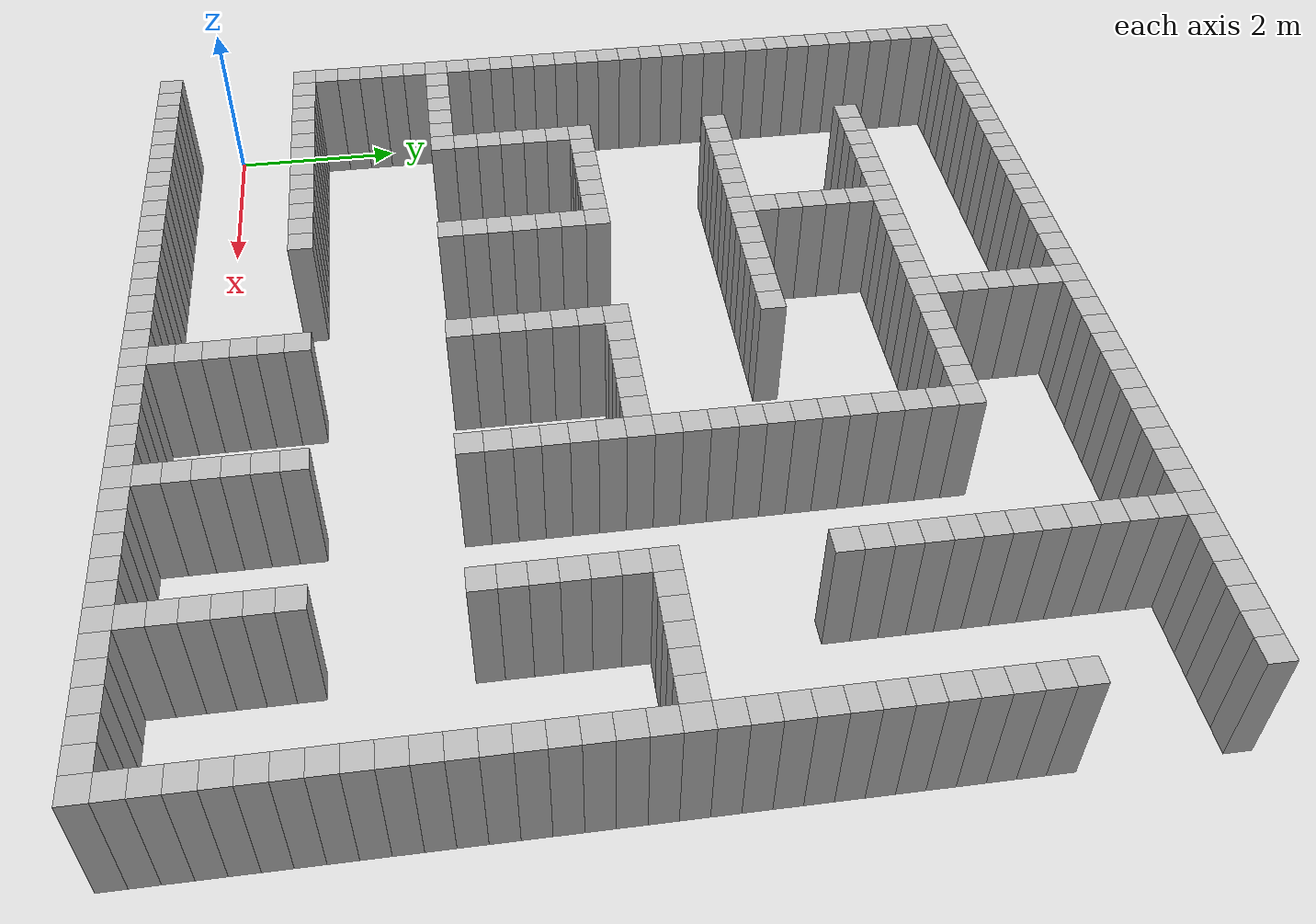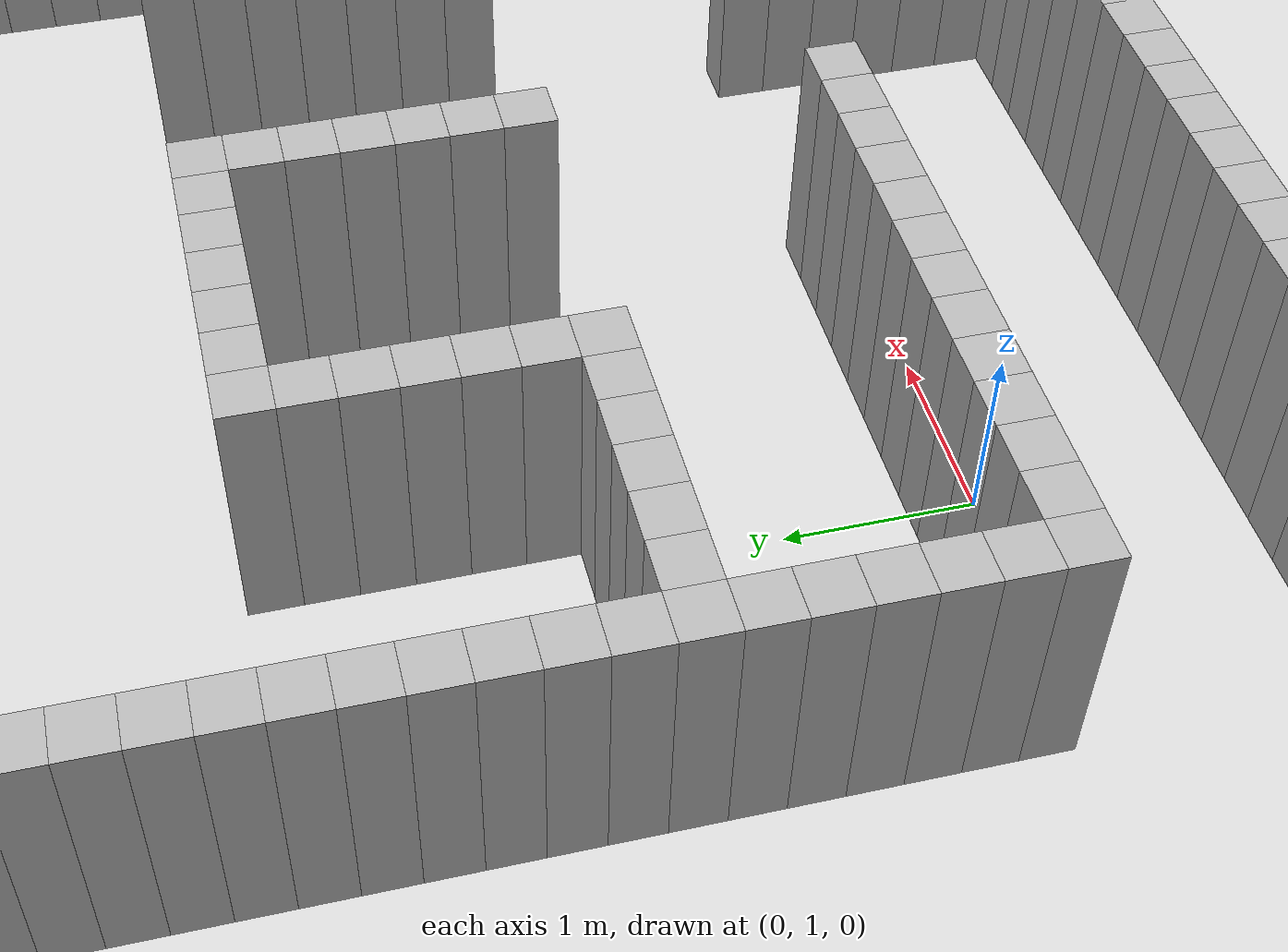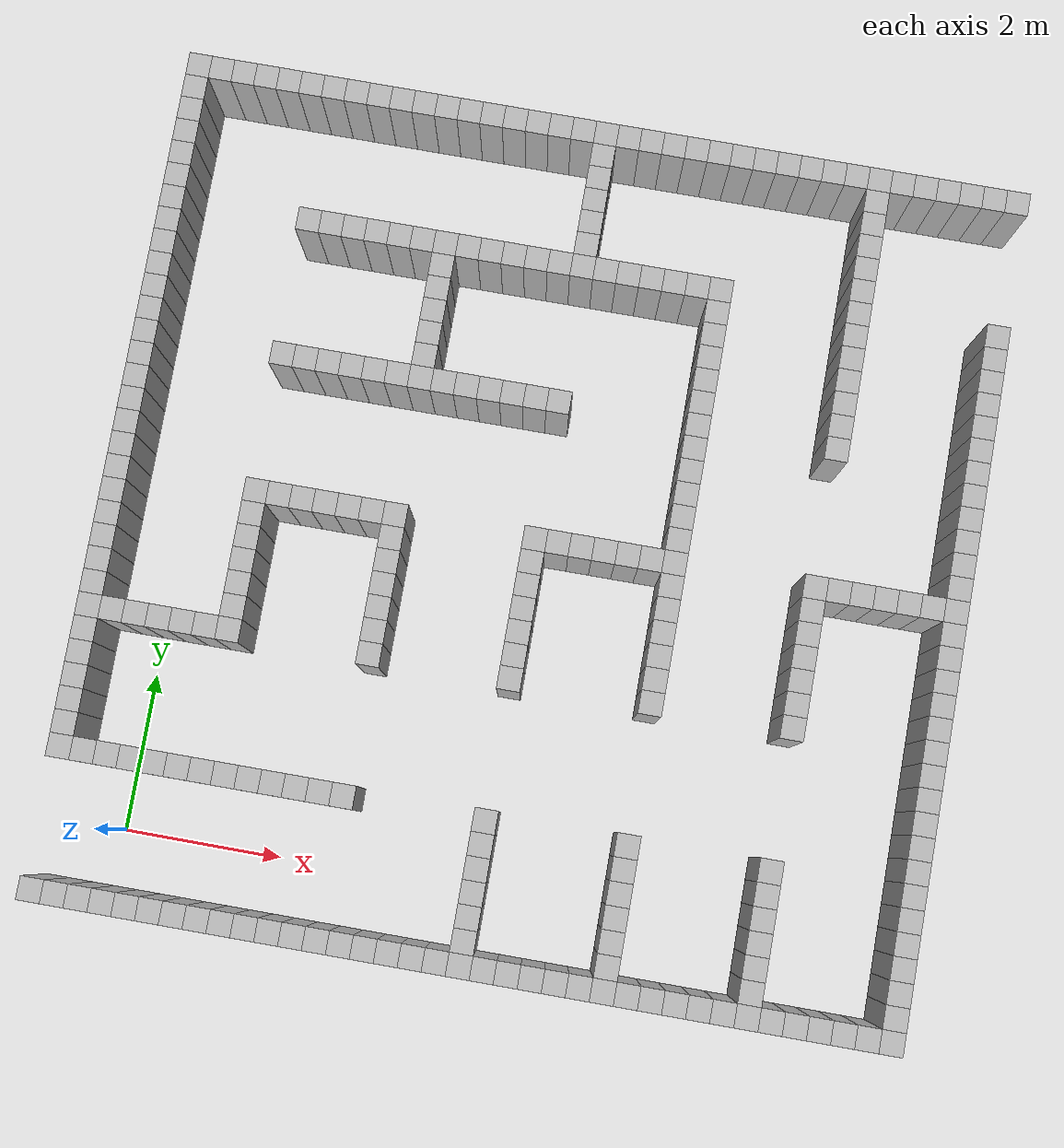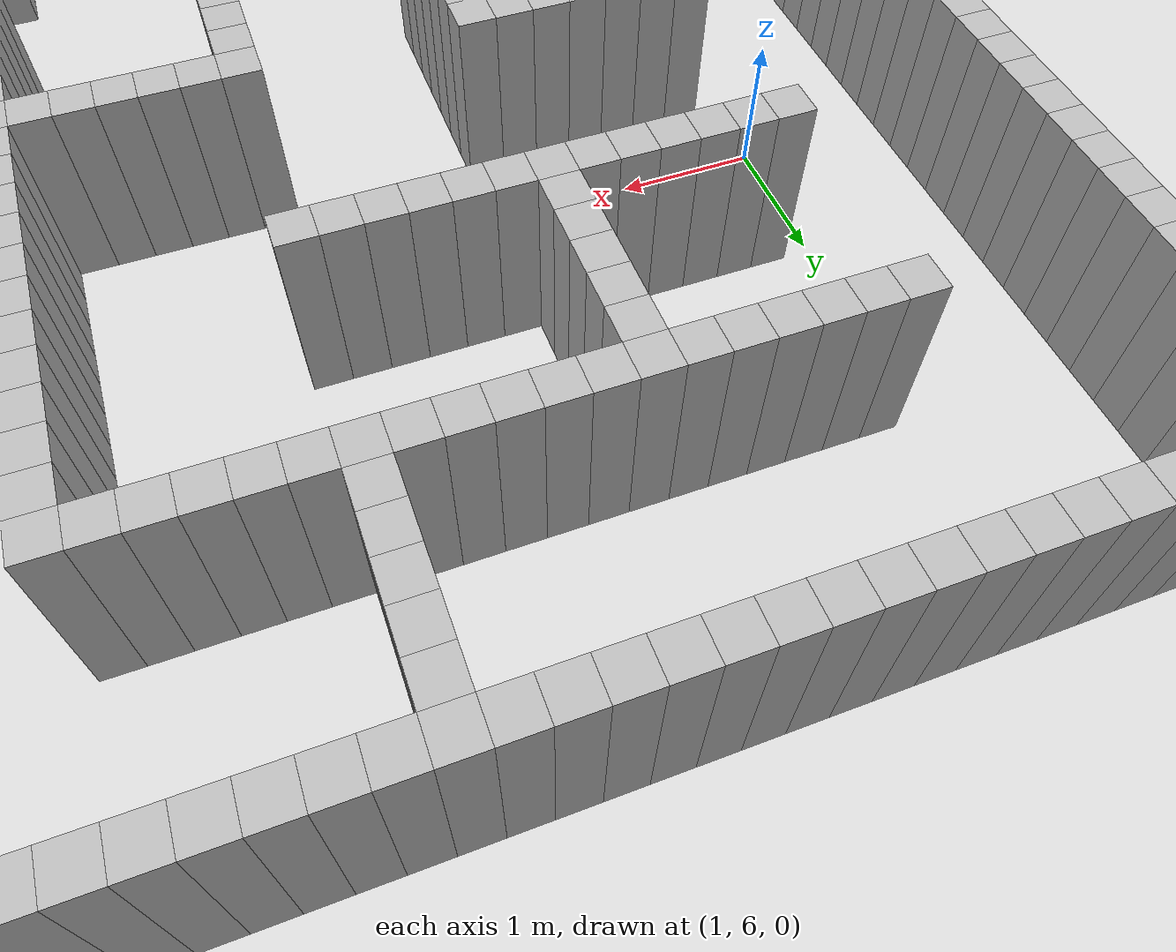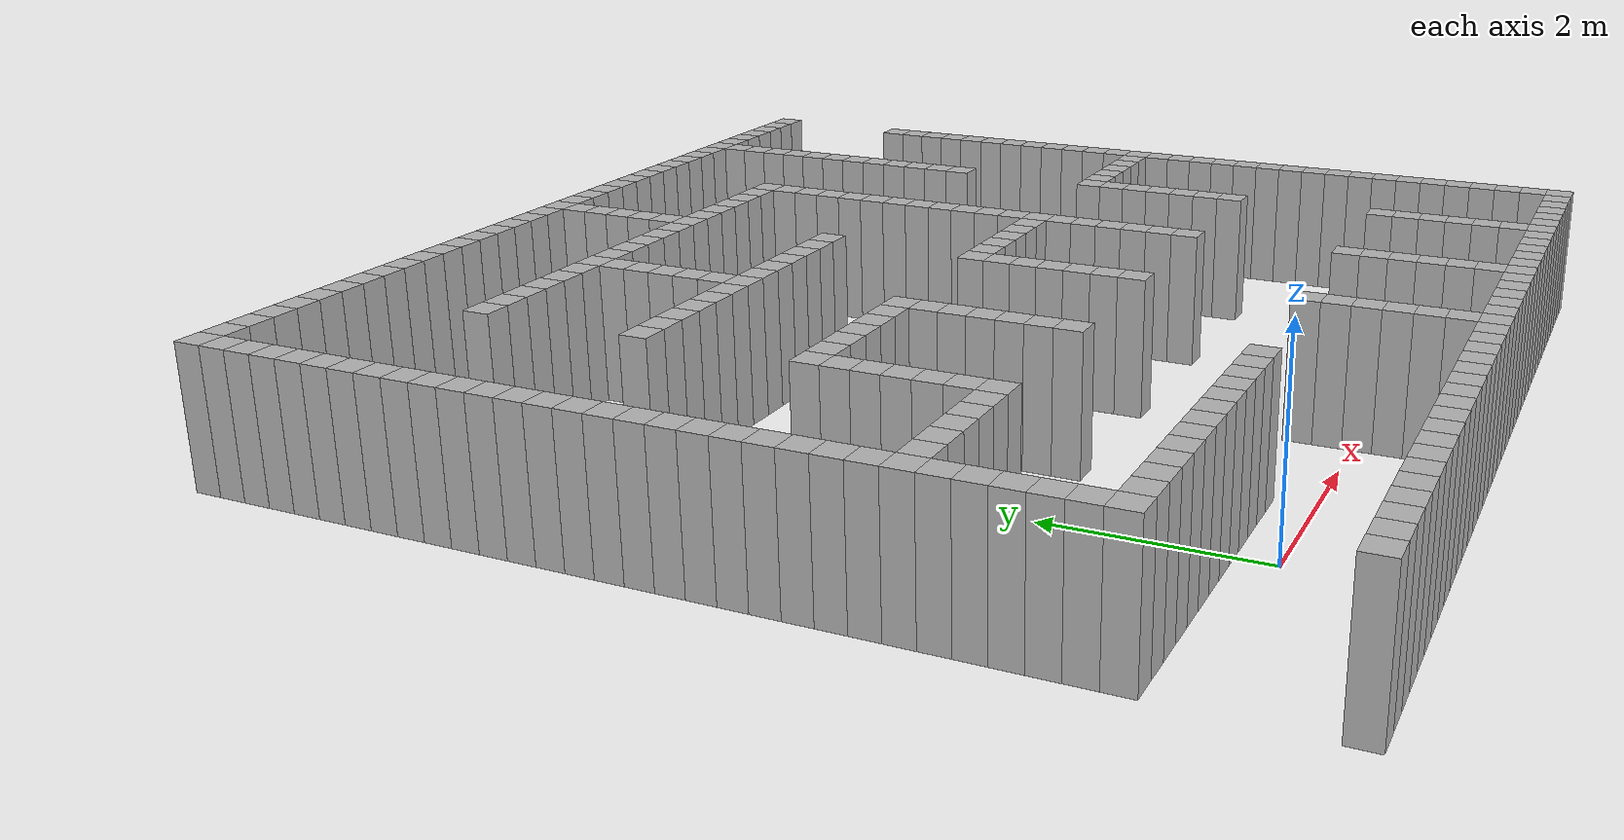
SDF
<sdf version="1.6">
<model name="Maze">
<pose>-1.2 -1.2 0 0 0 0 0</pose>
<link name="link_0">
<pose>0.3 0.3 0 0 0 0 0</pose>
<collision name="collision_0">
<geometry>
<box>
<size>0.3 0.3 1.5</size>
</box>
</geometry>
</collision>
<visual name="visual_0">
<geometry>
<box>
<size>0.3 0.3 1.5</size>
</box>
</geometry>
</visual>
</link>
<link name="link_1">
<pose>0.3 2.1 0 0 0 0 0</pose>
<collision name="collision_1">
<geometry>
<box>
<size>0.3 0.3 1.5</size>
</box>
</geometry>
</collision>
<visual name="visual_1">
<geometry>
<box>
<size>0.3 0.3 1.5</size>
</box>
</geometry>
</visual>
</link>
<link name="link_2">
<pose>0.3 2.4 0 0 0 0 0</pose>
<collision name="collision_2">
<geometry>
<box>
<size>0.3 0.3 1.5</size>
</box>
</geometry>
</collision>
<visual name="visual_2">
<geometry>
<box>
<size>0.3 0.3 1.5</size>
</box>
</geometry>
</visual>
</link>
<link name="link_3">
<pose>0.3 2.6999999999999997 0 0 0 0 0</pose>
<collision name="collision_3">
<geometry>
<box>
<size>0.3 0.3 1.5</size>
</box>
</geometry>
</collision>
<visual name="visual_3">
<geometry>
<box>
<size>0.3 0.3 1.5</size>
</box>
</geometry>
</visual>
</link>
<link name="link_4">
<pose>0.3 3.0 0 0 0 0 0</pose>
<collision name="collision_4">
<geometry>
<box>
<size>0.3 0.3 1.5</size>
</box>
</geometry>
</collision>
<visual name="visual_4">
<geometry>
<box>
<size>0.3 0.3 1.5</size>
</box>
</geometry>
</visual>
</link>
<link name="link_5">
<pose>0.3 3.3 0 0 0 0 0</pose>
<collision name="collision_5">
<geometry>
<box>
<size>0.3 0.3 1.5</size>
</box>
</geometry>
</collision>
<visual name="visual_5">
<geometry>
<box>
<size>0.3 0.3 1.5</size>
</box>
</geometry>
</visual>
</link>
<link name="link_6">
<pose>0.3 3.5999999999999996 0 0 0 0 0</pose>
<collision name="collision_6">
<geometry>
<box>
<size>0.3 0.3 1.5</size>
</box>
</geometry>
</collision>
<visual name="visual_6">
<geometry>
<box>
<size>0.3 0.3 1.5</size>
</box>
</geometry>
</visual>
</link>
<link name="link_7">
<pose>0.3 3.9 0 0 0 0 0</pose>
<collision name="collision_7">
<geometry>
<box>
<size>0.3 0.3 1.5</size>
</box>
</geometry>
</collision>
<visual name="visual_7">
<geometry>
<box>
<size>0.3 0.3 1.5</size>
</box>
</geometry>
</visual>
</link>
<link name="link_8">
<pose>0.3 4.2 0 0 0 0 0</pose>
<collision name="collision_8">
<geometry>
<box>
<size>0.3 0.3 1.5</size>
</box>
</geometry>
</collision>
<visual name="visual_8">
<geometry>
<box>
<size>0.3 0.3 1.5</size>
</box>
</geometry>
</visual>
</link>
<link name="link_9">
<pose>0.3 4.5 0 0 0 0 0</pose>
<collision name="collision_9">
<geometry>
<box>
<size>0.3 0.3 1.5</size>
</box>
</geometry>
</collision>
<visual name="visual_9">
<geometry>
<box>
<size>0.3 0.3 1.5</size>
</box>
</geometry>
</visual>
</link>
<link name="link_10">
<pose>0.3 4.8 0 0 0 0 0</pose>
<collision name="collision_10">
<geometry>
<box>
<size>0.3 0.3 1.5</size>
</box>
</geometry>
</collision>
<visual name="visual_10">
<geometry>
<box>
<size>0.3 0.3 1.5</size>
</box>
</geometry>
</visual>
</link>
<link name="link_11">
<pose>0.3 5.1 0 0 0 0 0</pose>
<collision name="collision_11">
<geometry>
<box>
<size>0.3 0.3 1.5</size>
</box>
</geometry>
</collision>
<visual name="visual_11">
<geometry>
<box>
<size>0.3 0.3 1.5</size>
</box>
</geometry>
</visual>
</link>
<link name="link_12">
<pose>0.3 5.3999999999999995 0 0 0 0 0</pose>
<collision name="collision_12">
<geometry>
<box>
<size>0.3 0.3 1.5</size>
</box>
</geometry>
</collision>
<visual name="visual_12">
<geometry>
<box>
<size>0.3 0.3 1.5</size>
</box>
</geometry>
</visual>
</link>
<link name="link_13">
<pose>0.3 5.7 0 0 0 0 0</pose>
<collision name="collision_13">
<geometry>
<box>
<size>0.3 0.3 1.5</size>
</box>
</geometry>
</collision>
<visual name="visual_13">
<geometry>
<box>
<size>0.3 0.3 1.5</size>
</box>
</geometry>
</visual>
</link>
<link name="link_14">
<pose>0.3 6.0 0 0 0 0 0</pose>
<collision name="collision_14">
<geometry>
<box>
<size>0.3 0.3 1.5</size>
</box>
</geometry>
</collision>
<visual name="visual_14">
<geometry>
<box>
<size>0.3 0.3 1.5</size>
</box>
</geometry>
</visual>
</link>
<link name="link_15">
<pose>0.3 6.3 0 0 0 0 0</pose>
<collision name="collision_15">
<geometry>
<box>
<size>0.3 0.3 1.5</size>
</box>
</geometry>
</collision>
<visual name="visual_15">
<geometry>
<box>
<size>0.3 0.3 1.5</size>
</box>
</geometry>
</visual>
</link>
<link name="link_16">
<pose>0.3 6.6 0 0 0 0 0</pose>
<collision name="collision_16">
<geometry>
<box>
<size>0.3 0.3 1.5</size>
</box>
</geometry>
</collision>
<visual name="visual_16">
<geometry>
<box>
<size>0.3 0.3 1.5</size>
</box>
</geometry>
</visual>
</link>
<link name="link_17">
<pose>0.3 6.8999999999999995 0 0 0 0 0</pose>
<collision name="collision_17">
<geometry>
<box>
<size>0.3 0.3 1.5</size>
</box>
</geometry>
</collision>
<visual name="visual_17">
<geometry>
<box>
<size>0.3 0.3 1.5</size>
</box>
</geometry>
</visual>
</link>
<link name="link_18">
<pose>0.3 7.199999999999999 0 0 0 0 0</pose>
<collision name="collision_18">
<geometry>
<box>
<size>0.3 0.3 1.5</size>
</box>
</geometry>
</collision>
<visual name="visual_18">
<geometry>
<box>
<size>0.3 0.3 1.5</size>
</box>
</geometry>
</visual>
</link>
<link name="link_19">
<pose>0.3 7.5 0 0 0 0 0</pose>
<collision name="collision_19">
<geometry>
<box>
<size>0.3 0.3 1.5</size>
</box>
</geometry>
</collision>
<visual name="visual_19">
<geometry>
<box>
<size>0.3 0.3 1.5</size>
</box>
</geometry>
</visual>
</link>
<link name="link_20">
<pose>0.3 7.8 0 0 0 0 0</pose>
<collision name="collision_20">
<geometry>
<box>
<size>0.3 0.3 1.5</size>
</box>
</geometry>
</collision>
<visual name="visual_20">
<geometry>
<box>
<size>0.3 0.3 1.5</size>
</box>
</geometry>
</visual>
</link>
<link name="link_21">
<pose>0.3 8.1 0 0 0 0 0</pose>
<collision name="collision_21">
<geometry>
<box>
<size>0.3 0.3 1.5</size>
</box>
</geometry>
</collision>
<visual name="visual_21">
<geometry>
<box>
<size>0.3 0.3 1.5</size>
</box>
</geometry>
</visual>
</link>
<link name="link_22">
<pose>0.3 8.4 0 0 0 0 0</pose>
<collision name="collision_22">
<geometry>
<box>
<size>0.3 0.3 1.5</size>
</box>
</geometry>
</collision>
<visual name="visual_22">
<geometry>
<box>
<size>0.3 0.3 1.5</size>
</box>
</geometry>
</visual>
</link>
<link name="link_23">
<pose>0.3 8.7 0 0 0 0 0</pose>
<collision name="collision_23">
<geometry>
<box>
<size>0.3 0.3 1.5</size>
</box>
</geometry>
</collision>
<visual name="visual_23">
<geometry>
<box>
<size>0.3 0.3 1.5</size>
</box>
</geometry>
</visual>
</link>
<link name="link_24">
<pose>0.3 9.0 0 0 0 0 0</pose>
<collision name="collision_24">
<geometry>
<box>
<size>0.3 0.3 1.5</size>
</box>
</geometry>
</collision>
<visual name="visual_24">
<geometry>
<box>
<size>0.3 0.3 1.5</size>
</box>
</geometry>
</visual>
</link>
<link name="link_25">
<pose>0.3 9.299999999999999 0 0 0 0 0</pose>
<collision name="collision_25">
<geometry>
<box>
<size>0.3 0.3 1.5</size>
</box>
</geometry>
</collision>
<visual name="visual_25">
<geometry>
<box>
<size>0.3 0.3 1.5</size>
</box>
</geometry>
</visual>
</link>
<link name="link_26">
<pose>0.3 9.6 0 0 0 0 0</pose>
<collision name="collision_26">
<geometry>
<box>
<size>0.3 0.3 1.5</size>
</box>
</geometry>
</collision>
<visual name="visual_26">
<geometry>
<box>
<size>0.3 0.3 1.5</size>
</box>
</geometry>
</visual>
</link>
<link name="link_27">
<pose>0.3 9.9 0 0 0 0 0</pose>
<collision name="collision_27">
<geometry>
<box>
<size>0.3 0.3 1.5</size>
</box>
</geometry>
</collision>
<visual name="visual_27">
<geometry>
<box>
<size>0.3 0.3 1.5</size>
</box>
</geometry>
</visual>
</link>
<link name="link_28">
<pose>0.3 10.2 0 0 0 0 0</pose>
<collision name="collision_28">
<geometry>
<box>
<size>0.3 0.3 1.5</size>
</box>
</geometry>
</collision>
<visual name="visual_28">
<geometry>
<box>
<size>0.3 0.3 1.5</size>
</box>
</geometry>
</visual>
</link>
<link name="link_29">
<pose>0.3 10.5 0 0 0 0 0</pose>
<collision name="collision_29">
<geometry>
<box>
<size>0.3 0.3 1.5</size>
</box>
</geometry>
</collision>
<visual name="visual_29">
<geometry>
<box>
<size>0.3 0.3 1.5</size>
</box>
</geometry>
</visual>
</link>
<link name="link_30">
<pose>0.3 10.799999999999999 0 0 0 0 0</pose>
<collision name="collision_30">
<geometry>
<box>
<size>0.3 0.3 1.5</size>
</box>
</geometry>
</collision>
<visual name="visual_30">
<geometry>
<box>
<size>0.3 0.3 1.5</size>
</box>
</geometry>
</visual>
</link>
<link name="link_31">
<pose>0.3 11.1 0 0 0 0 0</pose>
<collision name="collision_31">
<geometry>
<box>
<size>0.3 0.3 1.5</size>
</box>
</geometry>
</collision>
<visual name="visual_31">
<geometry>
<box>
<size>0.3 0.3 1.5</size>
</box>
</geometry>
</visual>
</link>
<link name="link_32">
<pose>0.6 0.3 0 0 0 0 0</pose>
<collision name="collision_32">
<geometry>
<box>
<size>0.3 0.3 1.5</size>
</box>
</geometry>
</collision>
<visual name="visual_32">
<geometry>
<box>
<size>0.3 0.3 1.5</size>
</box>
</geometry>
</visual>
</link>
<link name="link_33">
<pose>0.6 2.1 0 0 0 0 0</pose>
<collision name="collision_33">
<geometry>
<box>
<size>0.3 0.3 1.5</size>
</box>
</geometry>
</collision>
<visual name="visual_33">
<geometry>
<box>
<size>0.3 0.3 1.5</size>
</box>
</geometry>
</visual>
</link>
<link name="link_34">
<pose>0.6 3.9 0 0 0 0 0</pose>
<collision name="collision_34">
<geometry>
<box>
<size>0.3 0.3 1.5</size>
</box>
</geometry>
</collision>
<visual name="visual_34">
<geometry>
<box>
<size>0.3 0.3 1.5</size>
</box>
</geometry>
</visual>
</link>
<link name="link_35">
<pose>0.6 11.1 0 0 0 0 0</pose>
<collision name="collision_35">
<geometry>
<box>
<size>0.3 0.3 1.5</size>
</box>
</geometry>
</collision>
<visual name="visual_35">
<geometry>
<box>
<size>0.3 0.3 1.5</size>
</box>
</geometry>
</visual>
</link>
<link name="link_36">
<pose>0.8999999999999999 0.3 0 0 0 0 0</pose>
<collision name="collision_36">
<geometry>
<box>
<size>0.3 0.3 1.5</size>
</box>
</geometry>
</collision>
<visual name="visual_36">
<geometry>
<box>
<size>0.3 0.3 1.5</size>
</box>
</geometry>
</visual>
</link>
<link name="link_37">
<pose>0.8999999999999999 2.1 0 0 0 0 0</pose>
<collision name="collision_37">
<geometry>
<box>
<size>0.3 0.3 1.5</size>
</box>
</geometry>
</collision>
<visual name="visual_37">
<geometry>
<box>
<size>0.3 0.3 1.5</size>
</box>
</geometry>
</visual>
</link>
<link name="link_38">
<pose>0.8999999999999999 3.9 0 0 0 0 0</pose>
<collision name="collision_38">
<geometry>
<box>
<size>0.3 0.3 1.5</size>
</box>
</geometry>
</collision>
<visual name="visual_38">
<geometry>
<box>
<size>0.3 0.3 1.5</size>
</box>
</geometry>
</visual>
</link>
<link name="link_39">
<pose>0.8999999999999999 11.1 0 0 0 0 0</pose>
<collision name="collision_39">
<geometry>
<box>
<size>0.3 0.3 1.5</size>
</box>
</geometry>
</collision>
<visual name="visual_39">
<geometry>
<box>
<size>0.3 0.3 1.5</size>
</box>
</geometry>
</visual>
</link>
<link name="link_40">
<pose>1.2 0.3 0 0 0 0 0</pose>
<collision name="collision_40">
<geometry>
<box>
<size>0.3 0.3 1.5</size>
</box>
</geometry>
</collision>
<visual name="visual_40">
<geometry>
<box>
<size>0.3 0.3 1.5</size>
</box>
</geometry>
</visual>
</link>
<link name="link_41">
<pose>1.2 2.1 0 0 0 0 0</pose>
<collision name="collision_41">
<geometry>
<box>
<size>0.3 0.3 1.5</size>
</box>
</geometry>
</collision>
<visual name="visual_41">
<geometry>
<box>
<size>0.3 0.3 1.5</size>
</box>
</geometry>
</visual>
</link>
<link name="link_42">
<pose>1.2 3.9 0 0 0 0 0</pose>
<collision name="collision_42">
<geometry>
<box>
<size>0.3 0.3 1.5</size>
</box>
</geometry>
</collision>
<visual name="visual_42">
<geometry>
<box>
<size>0.3 0.3 1.5</size>
</box>
</geometry>
</visual>
</link>
<link name="link_43">
<pose>1.2 11.1 0 0 0 0 0</pose>
<collision name="collision_43">
<geometry>
<box>
<size>0.3 0.3 1.5</size>
</box>
</geometry>
</collision>
<visual name="visual_43">
<geometry>
<box>
<size>0.3 0.3 1.5</size>
</box>
</geometry>
</visual>
</link>
<link name="link_44">
<pose>1.5 0.3 0 0 0 0 0</pose>
<collision name="collision_44">
<geometry>
<box>
<size>0.3 0.3 1.5</size>
</box>
</geometry>
</collision>
<visual name="visual_44">
<geometry>
<box>
<size>0.3 0.3 1.5</size>
</box>
</geometry>
</visual>
</link>
<link name="link_45">
<pose>1.5 2.1 0 0 0 0 0</pose>
<collision name="collision_45">
<geometry>
<box>
<size>0.3 0.3 1.5</size>
</box>
</geometry>
</collision>
<visual name="visual_45">
<geometry>
<box>
<size>0.3 0.3 1.5</size>
</box>
</geometry>
</visual>
</link>
<link name="link_46">
<pose>1.5 3.9 0 0 0 0 0</pose>
<collision name="collision_46">
<geometry>
<box>
<size>0.3 0.3 1.5</size>
</box>
</geometry>
</collision>
<visual name="visual_46">
<geometry>
<box>
<size>0.3 0.3 1.5</size>
</box>
</geometry>
</visual>
</link>
<link name="link_47">
<pose>1.5 11.1 0 0 0 0 0</pose>
<collision name="collision_47">
<geometry>
<box>
<size>0.3 0.3 1.5</size>
</box>
</geometry>
</collision>
<visual name="visual_47">
<geometry>
<box>
<size>0.3 0.3 1.5</size>
</box>
</geometry>
</visual>
</link>
<link name="link_48">
<pose>1.7999999999999998 0.3 0 0 0 0 0</pose>
<collision name="collision_48">
<geometry>
<box>
<size>0.3 0.3 1.5</size>
</box>
</geometry>
</collision>
<visual name="visual_48">
<geometry>
<box>
<size>0.3 0.3 1.5</size>
</box>
</geometry>
</visual>
</link>
<link name="link_49">
<pose>1.7999999999999998 2.1 0 0 0 0 0</pose>
<collision name="collision_49">
<geometry>
<box>
<size>0.3 0.3 1.5</size>
</box>
</geometry>
</collision>
<visual name="visual_49">
<geometry>
<box>
<size>0.3 0.3 1.5</size>
</box>
</geometry>
</visual>
</link>
<link name="link_50">
<pose>1.7999999999999998 3.9 0 0 0 0 0</pose>
<collision name="collision_50">
<geometry>
<box>
<size>0.3 0.3 1.5</size>
</box>
</geometry>
</collision>
<visual name="visual_50">
<geometry>
<box>
<size>0.3 0.3 1.5</size>
</box>
</geometry>
</visual>
</link>
<link name="link_51">
<pose>1.7999999999999998 11.1 0 0 0 0 0</pose>
<collision name="collision_51">
<geometry>
<box>
<size>0.3 0.3 1.5</size>
</box>
</geometry>
</collision>
<visual name="visual_51">
<geometry>
<box>
<size>0.3 0.3 1.5</size>
</box>
</geometry>
</visual>
</link>
<link name="link_52">
<pose>2.1 0.3 0 0 0 0 0</pose>
<collision name="collision_52">
<geometry>
<box>
<size>0.3 0.3 1.5</size>
</box>
</geometry>
</collision>
<visual name="visual_52">
<geometry>
<box>
<size>0.3 0.3 1.5</size>
</box>
</geometry>
</visual>
</link>
<link name="link_53">
<pose>2.1 2.1 0 0 0 0 0</pose>
<collision name="collision_53">
<geometry>
<box>
<size>0.3 0.3 1.5</size>
</box>
</geometry>
</collision>
<visual name="visual_53">
<geometry>
<box>
<size>0.3 0.3 1.5</size>
</box>
</geometry>
</visual>
</link>
<link name="link_54">
<pose>2.1 3.9 0 0 0 0 0</pose>
<collision name="collision_54">
<geometry>
<box>
<size>0.3 0.3 1.5</size>
</box>
</geometry>
</collision>
<visual name="visual_54">
<geometry>
<box>
<size>0.3 0.3 1.5</size>
</box>
</geometry>
</visual>
</link>
<link name="link_55">
<pose>2.1 4.2 0 0 0 0 0</pose>
<collision name="collision_55">
<geometry>
<box>
<size>0.3 0.3 1.5</size>
</box>
</geometry>
</collision>
<visual name="visual_55">
<geometry>
<box>
<size>0.3 0.3 1.5</size>
</box>
</geometry>
</visual>
</link>
<link name="link_56">
<pose>2.1 4.5 0 0 0 0 0</pose>
<collision name="collision_56">
<geometry>
<box>
<size>0.3 0.3 1.5</size>
</box>
</geometry>
</collision>
<visual name="visual_56">
<geometry>
<box>
<size>0.3 0.3 1.5</size>
</box>
</geometry>
</visual>
</link>
<link name="link_57">
<pose>2.1 4.8 0 0 0 0 0</pose>
<collision name="collision_57">
<geometry>
<box>
<size>0.3 0.3 1.5</size>
</box>
</geometry>
</collision>
<visual name="visual_57">
<geometry>
<box>
<size>0.3 0.3 1.5</size>
</box>
</geometry>
</visual>
</link>
<link name="link_58">
<pose>2.1 5.1 0 0 0 0 0</pose>
<collision name="collision_58">
<geometry>
<box>
<size>0.3 0.3 1.5</size>
</box>
</geometry>
</collision>
<visual name="visual_58">
<geometry>
<box>
<size>0.3 0.3 1.5</size>
</box>
</geometry>
</visual>
</link>
<link name="link_59">
<pose>2.1 5.3999999999999995 0 0 0 0 0</pose>
<collision name="collision_59">
<geometry>
<box>
<size>0.3 0.3 1.5</size>
</box>
</geometry>
</collision>
<visual name="visual_59">
<geometry>
<box>
<size>0.3 0.3 1.5</size>
</box>
</geometry>
</visual>
</link>
<link name="link_60">
<pose>2.1 5.7 0 0 0 0 0</pose>
<collision name="collision_60">
<geometry>
<box>
<size>0.3 0.3 1.5</size>
</box>
</geometry>
</collision>
<visual name="visual_60">
<geometry>
<box>
<size>0.3 0.3 1.5</size>
</box>
</geometry>
</visual>
</link>
<link name="link_61">
<pose>2.1 7.5 0 0 0 0 0</pose>
<collision name="collision_61">
<geometry>
<box>
<size>0.3 0.3 1.5</size>
</box>
</geometry>
</collision>
<visual name="visual_61">
<geometry>
<box>
<size>0.3 0.3 1.5</size>
</box>
</geometry>
</visual>
</link>
<link name="link_62">
<pose>2.1 9.299999999999999 0 0 0 0 0</pose>
<collision name="collision_62">
<geometry>
<box>
<size>0.3 0.3 1.5</size>
</box>
</geometry>
</collision>
<visual name="visual_62">
<geometry>
<box>
<size>0.3 0.3 1.5</size>
</box>
</geometry>
</visual>
</link>
<link name="link_63">
<pose>2.1 11.1 0 0 0 0 0</pose>
<collision name="collision_63">
<geometry>
<box>
<size>0.3 0.3 1.5</size>
</box>
</geometry>
</collision>
<visual name="visual_63">
<geometry>
<box>
<size>0.3 0.3 1.5</size>
</box>
</geometry>
</visual>
</link>
<link name="link_64">
<pose>2.4 0.3 0 0 0 0 0</pose>
<collision name="collision_64">
<geometry>
<box>
<size>0.3 0.3 1.5</size>
</box>
</geometry>
</collision>
<visual name="visual_64">
<geometry>
<box>
<size>0.3 0.3 1.5</size>
</box>
</geometry>
</visual>
</link>
<link name="link_65">
<pose>2.4 2.1 0 0 0 0 0</pose>
<collision name="collision_65">
<geometry>
<box>
<size>0.3 0.3 1.5</size>
</box>
</geometry>
</collision>
<visual name="visual_65">
<geometry>
<box>
<size>0.3 0.3 1.5</size>
</box>
</geometry>
</visual>
</link>
<link name="link_66">
<pose>2.4 5.7 0 0 0 0 0</pose>
<collision name="collision_66">
<geometry>
<box>
<size>0.3 0.3 1.5</size>
</box>
</geometry>
</collision>
<visual name="visual_66">
<geometry>
<box>
<size>0.3 0.3 1.5</size>
</box>
</geometry>
</visual>
</link>
<link name="link_67">
<pose>2.4 7.5 0 0 0 0 0</pose>
<collision name="collision_67">
<geometry>
<box>
<size>0.3 0.3 1.5</size>
</box>
</geometry>
</collision>
<visual name="visual_67">
<geometry>
<box>
<size>0.3 0.3 1.5</size>
</box>
</geometry>
</visual>
</link>
<link name="link_68">
<pose>2.4 9.299999999999999 0 0 0 0 0</pose>
<collision name="collision_68">
<geometry>
<box>
<size>0.3 0.3 1.5</size>
</box>
</geometry>
</collision>
<visual name="visual_68">
<geometry>
<box>
<size>0.3 0.3 1.5</size>
</box>
</geometry>
</visual>
</link>
<link name="link_69">
<pose>2.4 11.1 0 0 0 0 0</pose>
<collision name="collision_69">
<geometry>
<box>
<size>0.3 0.3 1.5</size>
</box>
</geometry>
</collision>
<visual name="visual_69">
<geometry>
<box>
<size>0.3 0.3 1.5</size>
</box>
</geometry>
</visual>
</link>
<link name="link_70">
<pose>2.6999999999999997 0.3 0 0 0 0 0</pose>
<collision name="collision_70">
<geometry>
<box>
<size>0.3 0.3 1.5</size>
</box>
</geometry>
</collision>
<visual name="visual_70">
<geometry>
<box>
<size>0.3 0.3 1.5</size>
</box>
</geometry>
</visual>
</link>
<link name="link_71">
<pose>2.6999999999999997 2.1 0 0 0 0 0</pose>
<collision name="collision_71">
<geometry>
<box>
<size>0.3 0.3 1.5</size>
</box>
</geometry>
</collision>
<visual name="visual_71">
<geometry>
<box>
<size>0.3 0.3 1.5</size>
</box>
</geometry>
</visual>
</link>
<link name="link_72">
<pose>2.6999999999999997 5.7 0 0 0 0 0</pose>
<collision name="collision_72">
<geometry>
<box>
<size>0.3 0.3 1.5</size>
</box>
</geometry>
</collision>
<visual name="visual_72">
<geometry>
<box>
<size>0.3 0.3 1.5</size>
</box>
</geometry>
</visual>
</link>
<link name="link_73">
<pose>2.6999999999999997 7.5 0 0 0 0 0</pose>
<collision name="collision_73">
<geometry>
<box>
<size>0.3 0.3 1.5</size>
</box>
</geometry>
</collision>
<visual name="visual_73">
<geometry>
<box>
<size>0.3 0.3 1.5</size>
</box>
</geometry>
</visual>
</link>
<link name="link_74">
<pose>2.6999999999999997 9.299999999999999 0 0 0 0 0</pose>
<collision name="collision_74">
<geometry>
<box>
<size>0.3 0.3 1.5</size>
</box>
</geometry>
</collision>
<visual name="visual_74">
<geometry>
<box>
<size>0.3 0.3 1.5</size>
</box>
</geometry>
</visual>
</link>
<link name="link_75">
<pose>2.6999999999999997 11.1 0 0 0 0 0</pose>
<collision name="collision_75">
<geometry>
<box>
<size>0.3 0.3 1.5</size>
</box>
</geometry>
</collision>
<visual name="visual_75">
<geometry>
<box>
<size>0.3 0.3 1.5</size>
</box>
</geometry>
</visual>
</link>
<link name="link_76">
<pose>3.0 0.3 0 0 0 0 0</pose>
<collision name="collision_76">
<geometry>
<box>
<size>0.3 0.3 1.5</size>
</box>
</geometry>
</collision>
<visual name="visual_76">
<geometry>
<box>
<size>0.3 0.3 1.5</size>
</box>
</geometry>
</visual>
</link>
<link name="link_77">
<pose>3.0 2.1 0 0 0 0 0</pose>
<collision name="collision_77">
<geometry>
<box>
<size>0.3 0.3 1.5</size>
</box>
</geometry>
</collision>
<visual name="visual_77">
<geometry>
<box>
<size>0.3 0.3 1.5</size>
</box>
</geometry>
</visual>
</link>
<link name="link_78">
<pose>3.0 5.7 0 0 0 0 0</pose>
<collision name="collision_78">
<geometry>
<box>
<size>0.3 0.3 1.5</size>
</box>
</geometry>
</collision>
<visual name="visual_78">
<geometry>
<box>
<size>0.3 0.3 1.5</size>
</box>
</geometry>
</visual>
</link>
<link name="link_79">
<pose>3.0 7.5 0 0 0 0 0</pose>
<collision name="collision_79">
<geometry>
<box>
<size>0.3 0.3 1.5</size>
</box>
</geometry>
</collision>
<visual name="visual_79">
<geometry>
<box>
<size>0.3 0.3 1.5</size>
</box>
</geometry>
</visual>
</link>
<link name="link_80">
<pose>3.0 9.299999999999999 0 0 0 0 0</pose>
<collision name="collision_80">
<geometry>
<box>
<size>0.3 0.3 1.5</size>
</box>
</geometry>
</collision>
<visual name="visual_80">
<geometry>
<box>
<size>0.3 0.3 1.5</size>
</box>
</geometry>
</visual>
</link>
<link name="link_81">
<pose>3.0 11.1 0 0 0 0 0</pose>
<collision name="collision_81">
<geometry>
<box>
<size>0.3 0.3 1.5</size>
</box>
</geometry>
</collision>
<visual name="visual_81">
<geometry>
<box>
<size>0.3 0.3 1.5</size>
</box>
</geometry>
</visual>
</link>
<link name="link_82">
<pose>3.3 0.3 0 0 0 0 0</pose>
<collision name="collision_82">
<geometry>
<box>
<size>0.3 0.3 1.5</size>
</box>
</geometry>
</collision>
<visual name="visual_82">
<geometry>
<box>
<size>0.3 0.3 1.5</size>
</box>
</geometry>
</visual>
</link>
<link name="link_83">
<pose>3.3 2.1 0 0 0 0 0</pose>
<collision name="collision_83">
<geometry>
<box>
<size>0.3 0.3 1.5</size>
</box>
</geometry>
</collision>
<visual name="visual_83">
<geometry>
<box>
<size>0.3 0.3 1.5</size>
</box>
</geometry>
</visual>
</link>
<link name="link_84">
<pose>3.3 5.7 0 0 0 0 0</pose>
<collision name="collision_84">
<geometry>
<box>
<size>0.3 0.3 1.5</size>
</box>
</geometry>
</collision>
<visual name="visual_84">
<geometry>
<box>
<size>0.3 0.3 1.5</size>
</box>
</geometry>
</visual>
</link>
<link name="link_85">
<pose>3.3 7.5 0 0 0 0 0</pose>
<collision name="collision_85">
<geometry>
<box>
<size>0.3 0.3 1.5</size>
</box>
</geometry>
</collision>
<visual name="visual_85">
<geometry>
<box>
<size>0.3 0.3 1.5</size>
</box>
</geometry>
</visual>
</link>
<link name="link_86">
<pose>3.3 9.299999999999999 0 0 0 0 0</pose>
<collision name="collision_86">
<geometry>
<box>
<size>0.3 0.3 1.5</size>
</box>
</geometry>
</collision>
<visual name="visual_86">
<geometry>
<box>
<size>0.3 0.3 1.5</size>
</box>
</geometry>
</visual>
</link>
<link name="link_87">
<pose>3.3 11.1 0 0 0 0 0</pose>
<collision name="collision_87">
<geometry>
<box>
<size>0.3 0.3 1.5</size>
</box>
</geometry>
</collision>
<visual name="visual_87">
<geometry>
<box>
<size>0.3 0.3 1.5</size>
</box>
</geometry>
</visual>
</link>
<link name="link_88">
<pose>3.5999999999999996 0.3 0 0 0 0 0</pose>
<collision name="collision_88">
<geometry>
<box>
<size>0.3 0.3 1.5</size>
</box>
</geometry>
</collision>
<visual name="visual_88">
<geometry>
<box>
<size>0.3 0.3 1.5</size>
</box>
</geometry>
</visual>
</link>
<link name="link_89">
<pose>3.5999999999999996 2.1 0 0 0 0 0</pose>
<collision name="collision_89">
<geometry>
<box>
<size>0.3 0.3 1.5</size>
</box>
</geometry>
</collision>
<visual name="visual_89">
<geometry>
<box>
<size>0.3 0.3 1.5</size>
</box>
</geometry>
</visual>
</link>
<link name="link_90">
<pose>3.5999999999999996 5.7 0 0 0 0 0</pose>
<collision name="collision_90">
<geometry>
<box>
<size>0.3 0.3 1.5</size>
</box>
</geometry>
</collision>
<visual name="visual_90">
<geometry>
<box>
<size>0.3 0.3 1.5</size>
</box>
</geometry>
</visual>
</link>
<link name="link_91">
<pose>3.5999999999999996 7.5 0 0 0 0 0</pose>
<collision name="collision_91">
<geometry>
<box>
<size>0.3 0.3 1.5</size>
</box>
</geometry>
</collision>
<visual name="visual_91">
<geometry>
<box>
<size>0.3 0.3 1.5</size>
</box>
</geometry>
</visual>
</link>
<link name="link_92">
<pose>3.5999999999999996 9.299999999999999 0 0 0 0 0</pose>
<collision name="collision_92">
<geometry>
<box>
<size>0.3 0.3 1.5</size>
</box>
</geometry>
</collision>
<visual name="visual_92">
<geometry>
<box>
<size>0.3 0.3 1.5</size>
</box>
</geometry>
</visual>
</link>
<link name="link_93">
<pose>3.5999999999999996 11.1 0 0 0 0 0</pose>
<collision name="collision_93">
<geometry>
<box>
<size>0.3 0.3 1.5</size>
</box>
</geometry>
</collision>
<visual name="visual_93">
<geometry>
<box>
<size>0.3 0.3 1.5</size>
</box>
</geometry>
</visual>
</link>
<link name="link_94">
<pose>3.9 0.3 0 0 0 0 0</pose>
<collision name="collision_94">
<geometry>
<box>
<size>0.3 0.3 1.5</size>
</box>
</geometry>
</collision>
<visual name="visual_94">
<geometry>
<box>
<size>0.3 0.3 1.5</size>
</box>
</geometry>
</visual>
</link>
<link name="link_95">
<pose>3.9 2.1 0 0 0 0 0</pose>
<collision name="collision_95">
<geometry>
<box>
<size>0.3 0.3 1.5</size>
</box>
</geometry>
</collision>
<visual name="visual_95">
<geometry>
<box>
<size>0.3 0.3 1.5</size>
</box>
</geometry>
</visual>
</link>
<link name="link_96">
<pose>3.9 3.9 0 0 0 0 0</pose>
<collision name="collision_96">
<geometry>
<box>
<size>0.3 0.3 1.5</size>
</box>
</geometry>
</collision>
<visual name="visual_96">
<geometry>
<box>
<size>0.3 0.3 1.5</size>
</box>
</geometry>
</visual>
</link>
<link name="link_97">
<pose>3.9 4.2 0 0 0 0 0</pose>
<collision name="collision_97">
<geometry>
<box>
<size>0.3 0.3 1.5</size>
</box>
</geometry>
</collision>
<visual name="visual_97">
<geometry>
<box>
<size>0.3 0.3 1.5</size>
</box>
</geometry>
</visual>
</link>
<link name="link_98">
<pose>3.9 4.5 0 0 0 0 0</pose>
<collision name="collision_98">
<geometry>
<box>
<size>0.3 0.3 1.5</size>
</box>
</geometry>
</collision>
<visual name="visual_98">
<geometry>
<box>
<size>0.3 0.3 1.5</size>
</box>
</geometry>
</visual>
</link>
<link name="link_99">
<pose>3.9 4.8 0 0 0 0 0</pose>
<collision name="collision_99">
<geometry>
<box>
<size>0.3 0.3 1.5</size>
</box>
</geometry>
</collision>
<visual name="visual_99">
<geometry>
<box>
<size>0.3 0.3 1.5</size>
</box>
</geometry>
</visual>
</link>
<link name="link_100">
<pose>3.9 5.1 0 0 0 0 0</pose>
<collision name="collision_100">
<geometry>
<box>
<size>0.3 0.3 1.5</size>
</box>
</geometry>
</collision>
<visual name="visual_100">
<geometry>
<box>
<size>0.3 0.3 1.5</size>
</box>
</geometry>
</visual>
</link>
<link name="link_101">
<pose>3.9 5.3999999999999995 0 0 0 0 0</pose>
<collision name="collision_101">
<geometry>
<box>
<size>0.3 0.3 1.5</size>
</box>
</geometry>
</collision>
<visual name="visual_101">
<geometry>
<box>
<size>0.3 0.3 1.5</size>
</box>
</geometry>
</visual>
</link>
<link name="link_102">
<pose>3.9 5.7 0 0 0 0 0</pose>
<collision name="collision_102">
<geometry>
<box>
<size>0.3 0.3 1.5</size>
</box>
</geometry>
</collision>
<visual name="visual_102">
<geometry>
<box>
<size>0.3 0.3 1.5</size>
</box>
</geometry>
</visual>
</link>
<link name="link_103">
<pose>3.9 7.5 0 0 0 0 0</pose>
<collision name="collision_103">
<geometry>
<box>
<size>0.3 0.3 1.5</size>
</box>
</geometry>
</collision>
<visual name="visual_103">
<geometry>
<box>
<size>0.3 0.3 1.5</size>
</box>
</geometry>
</visual>
</link>
<link name="link_104">
<pose>3.9 7.8 0 0 0 0 0</pose>
<collision name="collision_104">
<geometry>
<box>
<size>0.3 0.3 1.5</size>
</box>
</geometry>
</collision>
<visual name="visual_104">
<geometry>
<box>
<size>0.3 0.3 1.5</size>
</box>
</geometry>
</visual>
</link>
<link name="link_105">
<pose>3.9 8.1 0 0 0 0 0</pose>
<collision name="collision_105">
<geometry>
<box>
<size>0.3 0.3 1.5</size>
</box>
</geometry>
</collision>
<visual name="visual_105">
<geometry>
<box>
<size>0.3 0.3 1.5</size>
</box>
</geometry>
</visual>
</link>
<link name="link_106">
<pose>3.9 8.4 0 0 0 0 0</pose>
<collision name="collision_106">
<geometry>
<box>
<size>0.3 0.3 1.5</size>
</box>
</geometry>
</collision>
<visual name="visual_106">
<geometry>
<box>
<size>0.3 0.3 1.5</size>
</box>
</geometry>
</visual>
</link>
<link name="link_107">
<pose>3.9 8.7 0 0 0 0 0</pose>
<collision name="collision_107">
<geometry>
<box>
<size>0.3 0.3 1.5</size>
</box>
</geometry>
</collision>
<visual name="visual_107">
<geometry>
<box>
<size>0.3 0.3 1.5</size>
</box>
</geometry>
</visual>
</link>
<link name="link_108">
<pose>3.9 9.0 0 0 0 0 0</pose>
<collision name="collision_108">
<geometry>
<box>
<size>0.3 0.3 1.5</size>
</box>
</geometry>
</collision>
<visual name="visual_108">
<geometry>
<box>
<size>0.3 0.3 1.5</size>
</box>
</geometry>
</visual>
</link>
<link name="link_109">
<pose>3.9 9.299999999999999 0 0 0 0 0</pose>
<collision name="collision_109">
<geometry>
<box>
<size>0.3 0.3 1.5</size>
</box>
</geometry>
</collision>
<visual name="visual_109">
<geometry>
<box>
<size>0.3 0.3 1.5</size>
</box>
</geometry>
</visual>
</link>
<link name="link_110">
<pose>3.9 11.1 0 0 0 0 0</pose>
<collision name="collision_110">
<geometry>
<box>
<size>0.3 0.3 1.5</size>
</box>
</geometry>
</collision>
<visual name="visual_110">
<geometry>
<box>
<size>0.3 0.3 1.5</size>
</box>
</geometry>
</visual>
</link>
<link name="link_111">
<pose>4.2 0.3 0 0 0 0 0</pose>
<collision name="collision_111">
<geometry>
<box>
<size>0.3 0.3 1.5</size>
</box>
</geometry>
</collision>
<visual name="visual_111">
<geometry>
<box>
<size>0.3 0.3 1.5</size>
</box>
</geometry>
</visual>
</link>
<link name="link_112">
<pose>4.2 7.5 0 0 0 0 0</pose>
<collision name="collision_112">
<geometry>
<box>
<size>0.3 0.3 1.5</size>
</box>
</geometry>
</collision>
<visual name="visual_112">
<geometry>
<box>
<size>0.3 0.3 1.5</size>
</box>
</geometry>
</visual>
</link>
<link name="link_113">
<pose>4.2 9.299999999999999 0 0 0 0 0</pose>
<collision name="collision_113">
<geometry>
<box>
<size>0.3 0.3 1.5</size>
</box>
</geometry>
</collision>
<visual name="visual_113">
<geometry>
<box>
<size>0.3 0.3 1.5</size>
</box>
</geometry>
</visual>
</link>
<link name="link_114">
<pose>4.2 11.1 0 0 0 0 0</pose>
<collision name="collision_114">
<geometry>
<box>
<size>0.3 0.3 1.5</size>
</box>
</geometry>
</collision>
<visual name="visual_114">
<geometry>
<box>
<size>0.3 0.3 1.5</size>
</box>
</geometry>
</visual>
</link>
<link name="link_115">
<pose>4.5 0.3 0 0 0 0 0</pose>
<collision name="collision_115">
<geometry>
<box>
<size>0.3 0.3 1.5</size>
</box>
</geometry>
</collision>
<visual name="visual_115">
<geometry>
<box>
<size>0.3 0.3 1.5</size>
</box>
</geometry>
</visual>
</link>
<link name="link_116">
<pose>4.5 7.5 0 0 0 0 0</pose>
<collision name="collision_116">
<geometry>
<box>
<size>0.3 0.3 1.5</size>
</box>
</geometry>
</collision>
<visual name="visual_116">
<geometry>
<box>
<size>0.3 0.3 1.5</size>
</box>
</geometry>
</visual>
</link>
<link name="link_117">
<pose>4.5 9.299999999999999 0 0 0 0 0</pose>
<collision name="collision_117">
<geometry>
<box>
<size>0.3 0.3 1.5</size>
</box>
</geometry>
</collision>
<visual name="visual_117">
<geometry>
<box>
<size>0.3 0.3 1.5</size>
</box>
</geometry>
</visual>
</link>
<link name="link_118">
<pose>4.5 11.1 0 0 0 0 0</pose>
<collision name="collision_118">
<geometry>
<box>
<size>0.3 0.3 1.5</size>
</box>
</geometry>
</collision>
<visual name="visual_118">
<geometry>
<box>
<size>0.3 0.3 1.5</size>
</box>
</geometry>
</visual>
</link>
<link name="link_119">
<pose>4.8 0.3 0 0 0 0 0</pose>
<collision name="collision_119">
<geometry>
<box>
<size>0.3 0.3 1.5</size>
</box>
</geometry>
</collision>
<visual name="visual_119">
<geometry>
<box>
<size>0.3 0.3 1.5</size>
</box>
</geometry>
</visual>
</link>
<link name="link_120">
<pose>4.8 7.5 0 0 0 0 0</pose>
<collision name="collision_120">
<geometry>
<box>
<size>0.3 0.3 1.5</size>
</box>
</geometry>
</collision>
<visual name="visual_120">
<geometry>
<box>
<size>0.3 0.3 1.5</size>
</box>
</geometry>
</visual>
</link>
<link name="link_121">
<pose>4.8 9.299999999999999 0 0 0 0 0</pose>
<collision name="collision_121">
<geometry>
<box>
<size>0.3 0.3 1.5</size>
</box>
</geometry>
</collision>
<visual name="visual_121">
<geometry>
<box>
<size>0.3 0.3 1.5</size>
</box>
</geometry>
</visual>
</link>
<link name="link_122">
<pose>4.8 11.1 0 0 0 0 0</pose>
<collision name="collision_122">
<geometry>
<box>
<size>0.3 0.3 1.5</size>
</box>
</geometry>
</collision>
<visual name="visual_122">
<geometry>
<box>
<size>0.3 0.3 1.5</size>
</box>
</geometry>
</visual>
</link>
<link name="link_123">
<pose>5.1 0.3 0 0 0 0 0</pose>
<collision name="collision_123">
<geometry>
<box>
<size>0.3 0.3 1.5</size>
</box>
</geometry>
</collision>
<visual name="visual_123">
<geometry>
<box>
<size>0.3 0.3 1.5</size>
</box>
</geometry>
</visual>
</link>
<link name="link_124">
<pose>5.1 7.5 0 0 0 0 0</pose>
<collision name="collision_124">
<geometry>
<box>
<size>0.3 0.3 1.5</size>
</box>
</geometry>
</collision>
<visual name="visual_124">
<geometry>
<box>
<size>0.3 0.3 1.5</size>
</box>
</geometry>
</visual>
</link>
<link name="link_125">
<pose>5.1 9.299999999999999 0 0 0 0 0</pose>
<collision name="collision_125">
<geometry>
<box>
<size>0.3 0.3 1.5</size>
</box>
</geometry>
</collision>
<visual name="visual_125">
<geometry>
<box>
<size>0.3 0.3 1.5</size>
</box>
</geometry>
</visual>
</link>
<link name="link_126">
<pose>5.1 11.1 0 0 0 0 0</pose>
<collision name="collision_126">
<geometry>
<box>
<size>0.3 0.3 1.5</size>
</box>
</geometry>
</collision>
<visual name="visual_126">
<geometry>
<box>
<size>0.3 0.3 1.5</size>
</box>
</geometry>
</visual>
</link>
<link name="link_127">
<pose>5.3999999999999995 0.3 0 0 0 0 0</pose>
<collision name="collision_127">
<geometry>
<box>
<size>0.3 0.3 1.5</size>
</box>
</geometry>
</collision>
<visual name="visual_127">
<geometry>
<box>
<size>0.3 0.3 1.5</size>
</box>
</geometry>
</visual>
</link>
<link name="link_128">
<pose>5.3999999999999995 7.5 0 0 0 0 0</pose>
<collision name="collision_128">
<geometry>
<box>
<size>0.3 0.3 1.5</size>
</box>
</geometry>
</collision>
<visual name="visual_128">
<geometry>
<box>
<size>0.3 0.3 1.5</size>
</box>
</geometry>
</visual>
</link>
<link name="link_129">
<pose>5.3999999999999995 9.299999999999999 0 0 0 0 0</pose>
<collision name="collision_129">
<geometry>
<box>
<size>0.3 0.3 1.5</size>
</box>
</geometry>
</collision>
<visual name="visual_129">
<geometry>
<box>
<size>0.3 0.3 1.5</size>
</box>
</geometry>
</visual>
</link>
<link name="link_130">
<pose>5.3999999999999995 11.1 0 0 0 0 0</pose>
<collision name="collision_130">
<geometry>
<box>
<size>0.3 0.3 1.5</size>
</box>
</geometry>
</collision>
<visual name="visual_130">
<geometry>
<box>
<size>0.3 0.3 1.5</size>
</box>
</geometry>
</visual>
</link>
<link name="link_131">
<pose>5.7 0.3 0 0 0 0 0</pose>
<collision name="collision_131">
<geometry>
<box>
<size>0.3 0.3 1.5</size>
</box>
</geometry>
</collision>
<visual name="visual_131">
<geometry>
<box>
<size>0.3 0.3 1.5</size>
</box>
</geometry>
</visual>
</link>
<link name="link_132">
<pose>5.7 0.6 0 0 0 0 0</pose>
<collision name="collision_132">
<geometry>
<box>
<size>0.3 0.3 1.5</size>
</box>
</geometry>
</collision>
<visual name="visual_132">
<geometry>
<box>
<size>0.3 0.3 1.5</size>
</box>
</geometry>
</visual>
</link>
<link name="link_133">
<pose>5.7 0.8999999999999999 0 0 0 0 0</pose>
<collision name="collision_133">
<geometry>
<box>
<size>0.3 0.3 1.5</size>
</box>
</geometry>
</collision>
<visual name="visual_133">
<geometry>
<box>
<size>0.3 0.3 1.5</size>
</box>
</geometry>
</visual>
</link>
<link name="link_134">
<pose>5.7 1.2 0 0 0 0 0</pose>
<collision name="collision_134">
<geometry>
<box>
<size>0.3 0.3 1.5</size>
</box>
</geometry>
</collision>
<visual name="visual_134">
<geometry>
<box>
<size>0.3 0.3 1.5</size>
</box>
</geometry>
</visual>
</link>
<link name="link_135">
<pose>5.7 1.5 0 0 0 0 0</pose>
<collision name="collision_135">
<geometry>
<box>
<size>0.3 0.3 1.5</size>
</box>
</geometry>
</collision>
<visual name="visual_135">
<geometry>
<box>
<size>0.3 0.3 1.5</size>
</box>
</geometry>
</visual>
</link>
<link name="link_136">
<pose>5.7 1.7999999999999998 0 0 0 0 0</pose>
<collision name="collision_136">
<geometry>
<box>
<size>0.3 0.3 1.5</size>
</box>
</geometry>
</collision>
<visual name="visual_136">
<geometry>
<box>
<size>0.3 0.3 1.5</size>
</box>
</geometry>
</visual>
</link>
<link name="link_137">
<pose>5.7 2.1 0 0 0 0 0</pose>
<collision name="collision_137">
<geometry>
<box>
<size>0.3 0.3 1.5</size>
</box>
</geometry>
</collision>
<visual name="visual_137">
<geometry>
<box>
<size>0.3 0.3 1.5</size>
</box>
</geometry>
</visual>
</link>
<link name="link_138">
<pose>5.7 3.9 0 0 0 0 0</pose>
<collision name="collision_138">
<geometry>
<box>
<size>0.3 0.3 1.5</size>
</box>
</geometry>
</collision>
<visual name="visual_138">
<geometry>
<box>
<size>0.3 0.3 1.5</size>
</box>
</geometry>
</visual>
</link>
<link name="link_139">
<pose>5.7 4.2 0 0 0 0 0</pose>
<collision name="collision_139">
<geometry>
<box>
<size>0.3 0.3 1.5</size>
</box>
</geometry>
</collision>
<visual name="visual_139">
<geometry>
<box>
<size>0.3 0.3 1.5</size>
</box>
</geometry>
</visual>
</link>
<link name="link_140">
<pose>5.7 4.5 0 0 0 0 0</pose>
<collision name="collision_140">
<geometry>
<box>
<size>0.3 0.3 1.5</size>
</box>
</geometry>
</collision>
<visual name="visual_140">
<geometry>
<box>
<size>0.3 0.3 1.5</size>
</box>
</geometry>
</visual>
</link>
<link name="link_141">
<pose>5.7 4.8 0 0 0 0 0</pose>
<collision name="collision_141">
<geometry>
<box>
<size>0.3 0.3 1.5</size>
</box>
</geometry>
</collision>
<visual name="visual_141">
<geometry>
<box>
<size>0.3 0.3 1.5</size>
</box>
</geometry>
</visual>
</link>
<link name="link_142">
<pose>5.7 5.1 0 0 0 0 0</pose>
<collision name="collision_142">
<geometry>
<box>
<size>0.3 0.3 1.5</size>
</box>
</geometry>
</collision>
<visual name="visual_142">
<geometry>
<box>
<size>0.3 0.3 1.5</size>
</box>
</geometry>
</visual>
</link>
<link name="link_143">
<pose>5.7 5.3999999999999995 0 0 0 0 0</pose>
<collision name="collision_143">
<geometry>
<box>
<size>0.3 0.3 1.5</size>
</box>
</geometry>
</collision>
<visual name="visual_143">
<geometry>
<box>
<size>0.3 0.3 1.5</size>
</box>
</geometry>
</visual>
</link>
<link name="link_144">
<pose>5.7 5.7 0 0 0 0 0</pose>
<collision name="collision_144">
<geometry>
<box>
<size>0.3 0.3 1.5</size>
</box>
</geometry>
</collision>
<visual name="visual_144">
<geometry>
<box>
<size>0.3 0.3 1.5</size>
</box>
</geometry>
</visual>
</link>
<link name="link_145">
<pose>5.7 7.5 0 0 0 0 0</pose>
<collision name="collision_145">
<geometry>
<box>
<size>0.3 0.3 1.5</size>
</box>
</geometry>
</collision>
<visual name="visual_145">
<geometry>
<box>
<size>0.3 0.3 1.5</size>
</box>
</geometry>
</visual>
</link>
<link name="link_146">
<pose>5.7 9.299999999999999 0 0 0 0 0</pose>
<collision name="collision_146">
<geometry>
<box>
<size>0.3 0.3 1.5</size>
</box>
</geometry>
</collision>
<visual name="visual_146">
<geometry>
<box>
<size>0.3 0.3 1.5</size>
</box>
</geometry>
</visual>
</link>
<link name="link_147">
<pose>5.7 9.6 0 0 0 0 0</pose>
<collision name="collision_147">
<geometry>
<box>
<size>0.3 0.3 1.5</size>
</box>
</geometry>
</collision>
<visual name="visual_147">
<geometry>
<box>
<size>0.3 0.3 1.5</size>
</box>
</geometry>
</visual>
</link>
<link name="link_148">
<pose>5.7 9.9 0 0 0 0 0</pose>
<collision name="collision_148">
<geometry>
<box>
<size>0.3 0.3 1.5</size>
</box>
</geometry>
</collision>
<visual name="visual_148">
<geometry>
<box>
<size>0.3 0.3 1.5</size>
</box>
</geometry>
</visual>
</link>
<link name="link_149">
<pose>5.7 10.2 0 0 0 0 0</pose>
<collision name="collision_149">
<geometry>
<box>
<size>0.3 0.3 1.5</size>
</box>
</geometry>
</collision>
<visual name="visual_149">
<geometry>
<box>
<size>0.3 0.3 1.5</size>
</box>
</geometry>
</visual>
</link>
<link name="link_150">
<pose>5.7 10.5 0 0 0 0 0</pose>
<collision name="collision_150">
<geometry>
<box>
<size>0.3 0.3 1.5</size>
</box>
</geometry>
</collision>
<visual name="visual_150">
<geometry>
<box>
<size>0.3 0.3 1.5</size>
</box>
</geometry>
</visual>
</link>
<link name="link_151">
<pose>5.7 10.799999999999999 0 0 0 0 0</pose>
<collision name="collision_151">
<geometry>
<box>
<size>0.3 0.3 1.5</size>
</box>
</geometry>
</collision>
<visual name="visual_151">
<geometry>
<box>
<size>0.3 0.3 1.5</size>
</box>
</geometry>
</visual>
</link>
<link name="link_152">
<pose>5.7 11.1 0 0 0 0 0</pose>
<collision name="collision_152">
<geometry>
<box>
<size>0.3 0.3 1.5</size>
</box>
</geometry>
</collision>
<visual name="visual_152">
<geometry>
<box>
<size>0.3 0.3 1.5</size>
</box>
</geometry>
</visual>
</link>
<link name="link_153">
<pose>6.0 0.3 0 0 0 0 0</pose>
<collision name="collision_153">
<geometry>
<box>
<size>0.3 0.3 1.5</size>
</box>
</geometry>
</collision>
<visual name="visual_153">
<geometry>
<box>
<size>0.3 0.3 1.5</size>
</box>
</geometry>
</visual>
</link>
<link name="link_154">
<pose>6.0 5.7 0 0 0 0 0</pose>
<collision name="collision_154">
<geometry>
<box>
<size>0.3 0.3 1.5</size>
</box>
</geometry>
</collision>
<visual name="visual_154">
<geometry>
<box>
<size>0.3 0.3 1.5</size>
</box>
</geometry>
</visual>
</link>
<link name="link_155">
<pose>6.0 9.299999999999999 0 0 0 0 0</pose>
<collision name="collision_155">
<geometry>
<box>
<size>0.3 0.3 1.5</size>
</box>
</geometry>
</collision>
<visual name="visual_155">
<geometry>
<box>
<size>0.3 0.3 1.5</size>
</box>
</geometry>
</visual>
</link>
<link name="link_156">
<pose>6.0 11.1 0 0 0 0 0</pose>
<collision name="collision_156">
<geometry>
<box>
<size>0.3 0.3 1.5</size>
</box>
</geometry>
</collision>
<visual name="visual_156">
<geometry>
<box>
<size>0.3 0.3 1.5</size>
</box>
</geometry>
</visual>
</link>
<link name="link_157">
<pose>6.3 0.3 0 0 0 0 0</pose>
<collision name="collision_157">
<geometry>
<box>
<size>0.3 0.3 1.5</size>
</box>
</geometry>
</collision>
<visual name="visual_157">
<geometry>
<box>
<size>0.3 0.3 1.5</size>
</box>
</geometry>
</visual>
</link>
<link name="link_158">
<pose>6.3 5.7 0 0 0 0 0</pose>
<collision name="collision_158">
<geometry>
<box>
<size>0.3 0.3 1.5</size>
</box>
</geometry>
</collision>
<visual name="visual_158">
<geometry>
<box>
<size>0.3 0.3 1.5</size>
</box>
</geometry>
</visual>
</link>
<link name="link_159">
<pose>6.3 9.299999999999999 0 0 0 0 0</pose>
<collision name="collision_159">
<geometry>
<box>
<size>0.3 0.3 1.5</size>
</box>
</geometry>
</collision>
<visual name="visual_159">
<geometry>
<box>
<size>0.3 0.3 1.5</size>
</box>
</geometry>
</visual>
</link>
<link name="link_160">
<pose>6.3 11.1 0 0 0 0 0</pose>
<collision name="collision_160">
<geometry>
<box>
<size>0.3 0.3 1.5</size>
</box>
</geometry>
</collision>
<visual name="visual_160">
<geometry>
<box>
<size>0.3 0.3 1.5</size>
</box>
</geometry>
</visual>
</link>
<link name="link_161">
<pose>6.6 0.3 0 0 0 0 0</pose>
<collision name="collision_161">
<geometry>
<box>
<size>0.3 0.3 1.5</size>
</box>
</geometry>
</collision>
<visual name="visual_161">
<geometry>
<box>
<size>0.3 0.3 1.5</size>
</box>
</geometry>
</visual>
</link>
<link name="link_162">
<pose>6.6 5.7 0 0 0 0 0</pose>
<collision name="collision_162">
<geometry>
<box>
<size>0.3 0.3 1.5</size>
</box>
</geometry>
</collision>
<visual name="visual_162">
<geometry>
<box>
<size>0.3 0.3 1.5</size>
</box>
</geometry>
</visual>
</link>
<link name="link_163">
<pose>6.6 9.299999999999999 0 0 0 0 0</pose>
<collision name="collision_163">
<geometry>
<box>
<size>0.3 0.3 1.5</size>
</box>
</geometry>
</collision>
<visual name="visual_163">
<geometry>
<box>
<size>0.3 0.3 1.5</size>
</box>
</geometry>
</visual>
</link>
<link name="link_164">
<pose>6.6 11.1 0 0 0 0 0</pose>
<collision name="collision_164">
<geometry>
<box>
<size>0.3 0.3 1.5</size>
</box>
</geometry>
</collision>
<visual name="visual_164">
<geometry>
<box>
<size>0.3 0.3 1.5</size>
</box>
</geometry>
</visual>
</link>
<link name="link_165">
<pose>6.8999999999999995 0.3 0 0 0 0 0</pose>
<collision name="collision_165">
<geometry>
<box>
<size>0.3 0.3 1.5</size>
</box>
</geometry>
</collision>
<visual name="visual_165">
<geometry>
<box>
<size>0.3 0.3 1.5</size>
</box>
</geometry>
</visual>
</link>
<link name="link_166">
<pose>6.8999999999999995 5.7 0 0 0 0 0</pose>
<collision name="collision_166">
<geometry>
<box>
<size>0.3 0.3 1.5</size>
</box>
</geometry>
</collision>
<visual name="visual_166">
<geometry>
<box>
<size>0.3 0.3 1.5</size>
</box>
</geometry>
</visual>
</link>
<link name="link_167">
<pose>6.8999999999999995 9.299999999999999 0 0 0 0 0</pose>
<collision name="collision_167">
<geometry>
<box>
<size>0.3 0.3 1.5</size>
</box>
</geometry>
</collision>
<visual name="visual_167">
<geometry>
<box>
<size>0.3 0.3 1.5</size>
</box>
</geometry>
</visual>
</link>
<link name="link_168">
<pose>6.8999999999999995 11.1 0 0 0 0 0</pose>
<collision name="collision_168">
<geometry>
<box>
<size>0.3 0.3 1.5</size>
</box>
</geometry>
</collision>
<visual name="visual_168">
<geometry>
<box>
<size>0.3 0.3 1.5</size>
</box>
</geometry>
</visual>
</link>
<link name="link_169">
<pose>7.199999999999999 0.3 0 0 0 0 0</pose>
<collision name="collision_169">
<geometry>
<box>
<size>0.3 0.3 1.5</size>
</box>
</geometry>
</collision>
<visual name="visual_169">
<geometry>
<box>
<size>0.3 0.3 1.5</size>
</box>
</geometry>
</visual>
</link>
<link name="link_170">
<pose>7.199999999999999 5.7 0 0 0 0 0</pose>
<collision name="collision_170">
<geometry>
<box>
<size>0.3 0.3 1.5</size>
</box>
</geometry>
</collision>
<visual name="visual_170">
<geometry>
<box>
<size>0.3 0.3 1.5</size>
</box>
</geometry>
</visual>
</link>
<link name="link_171">
<pose>7.199999999999999 9.299999999999999 0 0 0 0 0</pose>
<collision name="collision_171">
<geometry>
<box>
<size>0.3 0.3 1.5</size>
</box>
</geometry>
</collision>
<visual name="visual_171">
<geometry>
<box>
<size>0.3 0.3 1.5</size>
</box>
</geometry>
</visual>
</link>
<link name="link_172">
<pose>7.199999999999999 11.1 0 0 0 0 0</pose>
<collision name="collision_172">
<geometry>
<box>
<size>0.3 0.3 1.5</size>
</box>
</geometry>
</collision>
<visual name="visual_172">
<geometry>
<box>
<size>0.3 0.3 1.5</size>
</box>
</geometry>
</visual>
</link>
<link name="link_173">
<pose>7.5 0.3 0 0 0 0 0</pose>
<collision name="collision_173">
<geometry>
<box>
<size>0.3 0.3 1.5</size>
</box>
</geometry>
</collision>
<visual name="visual_173">
<geometry>
<box>
<size>0.3 0.3 1.5</size>
</box>
</geometry>
</visual>
</link>
<link name="link_174">
<pose>7.5 0.6 0 0 0 0 0</pose>
<collision name="collision_174">
<geometry>
<box>
<size>0.3 0.3 1.5</size>
</box>
</geometry>
</collision>
<visual name="visual_174">
<geometry>
<box>
<size>0.3 0.3 1.5</size>
</box>
</geometry>
</visual>
</link>
<link name="link_175">
<pose>7.5 0.8999999999999999 0 0 0 0 0</pose>
<collision name="collision_175">
<geometry>
<box>
<size>0.3 0.3 1.5</size>
</box>
</geometry>
</collision>
<visual name="visual_175">
<geometry>
<box>
<size>0.3 0.3 1.5</size>
</box>
</geometry>
</visual>
</link>
<link name="link_176">
<pose>7.5 1.2 0 0 0 0 0</pose>
<collision name="collision_176">
<geometry>
<box>
<size>0.3 0.3 1.5</size>
</box>
</geometry>
</collision>
<visual name="visual_176">
<geometry>
<box>
<size>0.3 0.3 1.5</size>
</box>
</geometry>
</visual>
</link>
<link name="link_177">
<pose>7.5 1.5 0 0 0 0 0</pose>
<collision name="collision_177">
<geometry>
<box>
<size>0.3 0.3 1.5</size>
</box>
</geometry>
</collision>
<visual name="visual_177">
<geometry>
<box>
<size>0.3 0.3 1.5</size>
</box>
</geometry>
</visual>
</link>
<link name="link_178">
<pose>7.5 1.7999999999999998 0 0 0 0 0</pose>
<collision name="collision_178">
<geometry>
<box>
<size>0.3 0.3 1.5</size>
</box>
</geometry>
</collision>
<visual name="visual_178">
<geometry>
<box>
<size>0.3 0.3 1.5</size>
</box>
</geometry>
</visual>
</link>
<link name="link_179">
<pose>7.5 2.1 0 0 0 0 0</pose>
<collision name="collision_179">
<geometry>
<box>
<size>0.3 0.3 1.5</size>
</box>
</geometry>
</collision>
<visual name="visual_179">
<geometry>
<box>
<size>0.3 0.3 1.5</size>
</box>
</geometry>
</visual>
</link>
<link name="link_180">
<pose>7.5 3.9 0 0 0 0 0</pose>
<collision name="collision_180">
<geometry>
<box>
<size>0.3 0.3 1.5</size>
</box>
</geometry>
</collision>
<visual name="visual_180">
<geometry>
<box>
<size>0.3 0.3 1.5</size>
</box>
</geometry>
</visual>
</link>
<link name="link_181">
<pose>7.5 4.2 0 0 0 0 0</pose>
<collision name="collision_181">
<geometry>
<box>
<size>0.3 0.3 1.5</size>
</box>
</geometry>
</collision>
<visual name="visual_181">
<geometry>
<box>
<size>0.3 0.3 1.5</size>
</box>
</geometry>
</visual>
</link>
<link name="link_182">
<pose>7.5 4.5 0 0 0 0 0</pose>
<collision name="collision_182">
<geometry>
<box>
<size>0.3 0.3 1.5</size>
</box>
</geometry>
</collision>
<visual name="visual_182">
<geometry>
<box>
<size>0.3 0.3 1.5</size>
</box>
</geometry>
</visual>
</link>
<link name="link_183">
<pose>7.5 4.8 0 0 0 0 0</pose>
<collision name="collision_183">
<geometry>
<box>
<size>0.3 0.3 1.5</size>
</box>
</geometry>
</collision>
<visual name="visual_183">
<geometry>
<box>
<size>0.3 0.3 1.5</size>
</box>
</geometry>
</visual>
</link>
<link name="link_184">
<pose>7.5 5.1 0 0 0 0 0</pose>
<collision name="collision_184">
<geometry>
<box>
<size>0.3 0.3 1.5</size>
</box>
</geometry>
</collision>
<visual name="visual_184">
<geometry>
<box>
<size>0.3 0.3 1.5</size>
</box>
</geometry>
</visual>
</link>
<link name="link_185">
<pose>7.5 5.3999999999999995 0 0 0 0 0</pose>
<collision name="collision_185">
<geometry>
<box>
<size>0.3 0.3 1.5</size>
</box>
</geometry>
</collision>
<visual name="visual_185">
<geometry>
<box>
<size>0.3 0.3 1.5</size>
</box>
</geometry>
</visual>
</link>
<link name="link_186">
<pose>7.5 5.7 0 0 0 0 0</pose>
<collision name="collision_186">
<geometry>
<box>
<size>0.3 0.3 1.5</size>
</box>
</geometry>
</collision>
<visual name="visual_186">
<geometry>
<box>
<size>0.3 0.3 1.5</size>
</box>
</geometry>
</visual>
</link>
<link name="link_187">
<pose>7.5 6.0 0 0 0 0 0</pose>
<collision name="collision_187">
<geometry>
<box>
<size>0.3 0.3 1.5</size>
</box>
</geometry>
</collision>
<visual name="visual_187">
<geometry>
<box>
<size>0.3 0.3 1.5</size>
</box>
</geometry>
</visual>
</link>
<link name="link_188">
<pose>7.5 6.3 0 0 0 0 0</pose>
<collision name="collision_188">
<geometry>
<box>
<size>0.3 0.3 1.5</size>
</box>
</geometry>
</collision>
<visual name="visual_188">
<geometry>
<box>
<size>0.3 0.3 1.5</size>
</box>
</geometry>
</visual>
</link>
<link name="link_189">
<pose>7.5 6.6 0 0 0 0 0</pose>
<collision name="collision_189">
<geometry>
<box>
<size>0.3 0.3 1.5</size>
</box>
</geometry>
</collision>
<visual name="visual_189">
<geometry>
<box>
<size>0.3 0.3 1.5</size>
</box>
</geometry>
</visual>
</link>
<link name="link_190">
<pose>7.5 6.8999999999999995 0 0 0 0 0</pose>
<collision name="collision_190">
<geometry>
<box>
<size>0.3 0.3 1.5</size>
</box>
</geometry>
</collision>
<visual name="visual_190">
<geometry>
<box>
<size>0.3 0.3 1.5</size>
</box>
</geometry>
</visual>
</link>
<link name="link_191">
<pose>7.5 7.199999999999999 0 0 0 0 0</pose>
<collision name="collision_191">
<geometry>
<box>
<size>0.3 0.3 1.5</size>
</box>
</geometry>
</collision>
<visual name="visual_191">
<geometry>
<box>
<size>0.3 0.3 1.5</size>
</box>
</geometry>
</visual>
</link>
<link name="link_192">
<pose>7.5 7.5 0 0 0 0 0</pose>
<collision name="collision_192">
<geometry>
<box>
<size>0.3 0.3 1.5</size>
</box>
</geometry>
</collision>
<visual name="visual_192">
<geometry>
<box>
<size>0.3 0.3 1.5</size>
</box>
</geometry>
</visual>
</link>
<link name="link_193">
<pose>7.5 7.8 0 0 0 0 0</pose>
<collision name="collision_193">
<geometry>
<box>
<size>0.3 0.3 1.5</size>
</box>
</geometry>
</collision>
<visual name="visual_193">
<geometry>
<box>
<size>0.3 0.3 1.5</size>
</box>
</geometry>
</visual>
</link>
<link name="link_194">
<pose>7.5 8.1 0 0 0 0 0</pose>
<collision name="collision_194">
<geometry>
<box>
<size>0.3 0.3 1.5</size>
</box>
</geometry>
</collision>
<visual name="visual_194">
<geometry>
<box>
<size>0.3 0.3 1.5</size>
</box>
</geometry>
</visual>
</link>
<link name="link_195">
<pose>7.5 8.4 0 0 0 0 0</pose>
<collision name="collision_195">
<geometry>
<box>
<size>0.3 0.3 1.5</size>
</box>
</geometry>
</collision>
<visual name="visual_195">
<geometry>
<box>
<size>0.3 0.3 1.5</size>
</box>
</geometry>
</visual>
</link>
<link name="link_196">
<pose>7.5 8.7 0 0 0 0 0</pose>
<collision name="collision_196">
<geometry>
<box>
<size>0.3 0.3 1.5</size>
</box>
</geometry>
</collision>
<visual name="visual_196">
<geometry>
<box>
<size>0.3 0.3 1.5</size>
</box>
</geometry>
</visual>
</link>
<link name="link_197">
<pose>7.5 9.0 0 0 0 0 0</pose>
<collision name="collision_197">
<geometry>
<box>
<size>0.3 0.3 1.5</size>
</box>
</geometry>
</collision>
<visual name="visual_197">
<geometry>
<box>
<size>0.3 0.3 1.5</size>
</box>
</geometry>
</visual>
</link>
<link name="link_198">
<pose>7.5 9.299999999999999 0 0 0 0 0</pose>
<collision name="collision_198">
<geometry>
<box>
<size>0.3 0.3 1.5</size>
</box>
</geometry>
</collision>
<visual name="visual_198">
<geometry>
<box>
<size>0.3 0.3 1.5</size>
</box>
</geometry>
</visual>
</link>
<link name="link_199">
<pose>7.5 11.1 0 0 0 0 0</pose>
<collision name="collision_199">
<geometry>
<box>
<size>0.3 0.3 1.5</size>
</box>
</geometry>
</collision>
<visual name="visual_199">
<geometry>
<box>
<size>0.3 0.3 1.5</size>
</box>
</geometry>
</visual>
</link>
<link name="link_200">
<pose>7.8 0.3 0 0 0 0 0</pose>
<collision name="collision_200">
<geometry>
<box>
<size>0.3 0.3 1.5</size>
</box>
</geometry>
</collision>
<visual name="visual_200">
<geometry>
<box>
<size>0.3 0.3 1.5</size>
</box>
</geometry>
</visual>
</link>
<link name="link_201">
<pose>7.8 11.1 0 0 0 0 0</pose>
<collision name="collision_201">
<geometry>
<box>
<size>0.3 0.3 1.5</size>
</box>
</geometry>
</collision>
<visual name="visual_201">
<geometry>
<box>
<size>0.3 0.3 1.5</size>
</box>
</geometry>
</visual>
</link>
<link name="link_202">
<pose>8.1 0.3 0 0 0 0 0</pose>
<collision name="collision_202">
<geometry>
<box>
<size>0.3 0.3 1.5</size>
</box>
</geometry>
</collision>
<visual name="visual_202">
<geometry>
<box>
<size>0.3 0.3 1.5</size>
</box>
</geometry>
</visual>
</link>
<link name="link_203">
<pose>8.1 11.1 0 0 0 0 0</pose>
<collision name="collision_203">
<geometry>
<box>
<size>0.3 0.3 1.5</size>
</box>
</geometry>
</collision>
<visual name="visual_203">
<geometry>
<box>
<size>0.3 0.3 1.5</size>
</box>
</geometry>
</visual>
</link>
<link name="link_204">
<pose>8.4 0.3 0 0 0 0 0</pose>
<collision name="collision_204">
<geometry>
<box>
<size>0.3 0.3 1.5</size>
</box>
</geometry>
</collision>
<visual name="visual_204">
<geometry>
<box>
<size>0.3 0.3 1.5</size>
</box>
</geometry>
</visual>
</link>
<link name="link_205">
<pose>8.4 11.1 0 0 0 0 0</pose>
<collision name="collision_205">
<geometry>
<box>
<size>0.3 0.3 1.5</size>
</box>
</geometry>
</collision>
<visual name="visual_205">
<geometry>
<box>
<size>0.3 0.3 1.5</size>
</box>
</geometry>
</visual>
</link>
<link name="link_206">
<pose>8.7 0.3 0 0 0 0 0</pose>
<collision name="collision_206">
<geometry>
<box>
<size>0.3 0.3 1.5</size>
</box>
</geometry>
</collision>
<visual name="visual_206">
<geometry>
<box>
<size>0.3 0.3 1.5</size>
</box>
</geometry>
</visual>
</link>
<link name="link_207">
<pose>8.7 11.1 0 0 0 0 0</pose>
<collision name="collision_207">
<geometry>
<box>
<size>0.3 0.3 1.5</size>
</box>
</geometry>
</collision>
<visual name="visual_207">
<geometry>
<box>
<size>0.3 0.3 1.5</size>
</box>
</geometry>
</visual>
</link>
<link name="link_208">
<pose>9.0 0.3 0 0 0 0 0</pose>
<collision name="collision_208">
<geometry>
<box>
<size>0.3 0.3 1.5</size>
</box>
</geometry>
</collision>
<visual name="visual_208">
<geometry>
<box>
<size>0.3 0.3 1.5</size>
</box>
</geometry>
</visual>
</link>
<link name="link_209">
<pose>9.0 11.1 0 0 0 0 0</pose>
<collision name="collision_209">
<geometry>
<box>
<size>0.3 0.3 1.5</size>
</box>
</geometry>
</collision>
<visual name="visual_209">
<geometry>
<box>
<size>0.3 0.3 1.5</size>
</box>
</geometry>
</visual>
</link>
<link name="link_210">
<pose>9.299999999999999 0.3 0 0 0 0 0</pose>
<collision name="collision_210">
<geometry>
<box>
<size>0.3 0.3 1.5</size>
</box>
</geometry>
</collision>
<visual name="visual_210">
<geometry>
<box>
<size>0.3 0.3 1.5</size>
</box>
</geometry>
</visual>
</link>
<link name="link_211">
<pose>9.299999999999999 0.6 0 0 0 0 0</pose>
<collision name="collision_211">
<geometry>
<box>
<size>0.3 0.3 1.5</size>
</box>
</geometry>
</collision>
<visual name="visual_211">
<geometry>
<box>
<size>0.3 0.3 1.5</size>
</box>
</geometry>
</visual>
</link>
<link name="link_212">
<pose>9.299999999999999 0.8999999999999999 0 0 0 0 0</pose>
<collision name="collision_212">
<geometry>
<box>
<size>0.3 0.3 1.5</size>
</box>
</geometry>
</collision>
<visual name="visual_212">
<geometry>
<box>
<size>0.3 0.3 1.5</size>
</box>
</geometry>
</visual>
</link>
<link name="link_213">
<pose>9.299999999999999 1.2 0 0 0 0 0</pose>
<collision name="collision_213">
<geometry>
<box>
<size>0.3 0.3 1.5</size>
</box>
</geometry>
</collision>
<visual name="visual_213">
<geometry>
<box>
<size>0.3 0.3 1.5</size>
</box>
</geometry>
</visual>
</link>
<link name="link_214">
<pose>9.299999999999999 1.5 0 0 0 0 0</pose>
<collision name="collision_214">
<geometry>
<box>
<size>0.3 0.3 1.5</size>
</box>
</geometry>
</collision>
<visual name="visual_214">
<geometry>
<box>
<size>0.3 0.3 1.5</size>
</box>
</geometry>
</visual>
</link>
<link name="link_215">
<pose>9.299999999999999 1.7999999999999998 0 0 0 0 0</pose>
<collision name="collision_215">
<geometry>
<box>
<size>0.3 0.3 1.5</size>
</box>
</geometry>
</collision>
<visual name="visual_215">
<geometry>
<box>
<size>0.3 0.3 1.5</size>
</box>
</geometry>
</visual>
</link>
<link name="link_216">
<pose>9.299999999999999 2.1 0 0 0 0 0</pose>
<collision name="collision_216">
<geometry>
<box>
<size>0.3 0.3 1.5</size>
</box>
</geometry>
</collision>
<visual name="visual_216">
<geometry>
<box>
<size>0.3 0.3 1.5</size>
</box>
</geometry>
</visual>
</link>
<link name="link_217">
<pose>9.299999999999999 3.9 0 0 0 0 0</pose>
<collision name="collision_217">
<geometry>
<box>
<size>0.3 0.3 1.5</size>
</box>
</geometry>
</collision>
<visual name="visual_217">
<geometry>
<box>
<size>0.3 0.3 1.5</size>
</box>
</geometry>
</visual>
</link>
<link name="link_218">
<pose>9.299999999999999 4.2 0 0 0 0 0</pose>
<collision name="collision_218">
<geometry>
<box>
<size>0.3 0.3 1.5</size>
</box>
</geometry>
</collision>
<visual name="visual_218">
<geometry>
<box>
<size>0.3 0.3 1.5</size>
</box>
</geometry>
</visual>
</link>
<link name="link_219">
<pose>9.299999999999999 4.5 0 0 0 0 0</pose>
<collision name="collision_219">
<geometry>
<box>
<size>0.3 0.3 1.5</size>
</box>
</geometry>
</collision>
<visual name="visual_219">
<geometry>
<box>
<size>0.3 0.3 1.5</size>
</box>
</geometry>
</visual>
</link>
<link name="link_220">
<pose>9.299999999999999 4.8 0 0 0 0 0</pose>
<collision name="collision_220">
<geometry>
<box>
<size>0.3 0.3 1.5</size>
</box>
</geometry>
</collision>
<visual name="visual_220">
<geometry>
<box>
<size>0.3 0.3 1.5</size>
</box>
</geometry>
</visual>
</link>
<link name="link_221">
<pose>9.299999999999999 5.1 0 0 0 0 0</pose>
<collision name="collision_221">
<geometry>
<box>
<size>0.3 0.3 1.5</size>
</box>
</geometry>
</collision>
<visual name="visual_221">
<geometry>
<box>
<size>0.3 0.3 1.5</size>
</box>
</geometry>
</visual>
</link>
<link name="link_222">
<pose>9.299999999999999 5.3999999999999995 0 0 0 0 0</pose>
<collision name="collision_222">
<geometry>
<box>
<size>0.3 0.3 1.5</size>
</box>
</geometry>
</collision>
<visual name="visual_222">
<geometry>
<box>
<size>0.3 0.3 1.5</size>
</box>
</geometry>
</visual>
</link>
<link name="link_223">
<pose>9.299999999999999 5.7 0 0 0 0 0</pose>
<collision name="collision_223">
<geometry>
<box>
<size>0.3 0.3 1.5</size>
</box>
</geometry>
</collision>
<visual name="visual_223">
<geometry>
<box>
<size>0.3 0.3 1.5</size>
</box>
</geometry>
</visual>
</link>
<link name="link_224">
<pose>9.299999999999999 7.5 0 0 0 0 0</pose>
<collision name="collision_224">
<geometry>
<box>
<size>0.3 0.3 1.5</size>
</box>
</geometry>
</collision>
<visual name="visual_224">
<geometry>
<box>
<size>0.3 0.3 1.5</size>
</box>
</geometry>
</visual>
</link>
<link name="link_225">
<pose>9.299999999999999 7.8 0 0 0 0 0</pose>
<collision name="collision_225">
<geometry>
<box>
<size>0.3 0.3 1.5</size>
</box>
</geometry>
</collision>
<visual name="visual_225">
<geometry>
<box>
<size>0.3 0.3 1.5</size>
</box>
</geometry>
</visual>
</link>
<link name="link_226">
<pose>9.299999999999999 8.1 0 0 0 0 0</pose>
<collision name="collision_226">
<geometry>
<box>
<size>0.3 0.3 1.5</size>
</box>
</geometry>
</collision>
<visual name="visual_226">
<geometry>
<box>
<size>0.3 0.3 1.5</size>
</box>
</geometry>
</visual>
</link>
<link name="link_227">
<pose>9.299999999999999 8.4 0 0 0 0 0</pose>
<collision name="collision_227">
<geometry>
<box>
<size>0.3 0.3 1.5</size>
</box>
</geometry>
</collision>
<visual name="visual_227">
<geometry>
<box>
<size>0.3 0.3 1.5</size>
</box>
</geometry>
</visual>
</link>
<link name="link_228">
<pose>9.299999999999999 8.7 0 0 0 0 0</pose>
<collision name="collision_228">
<geometry>
<box>
<size>0.3 0.3 1.5</size>
</box>
</geometry>
</collision>
<visual name="visual_228">
<geometry>
<box>
<size>0.3 0.3 1.5</size>
</box>
</geometry>
</visual>
</link>
<link name="link_229">
<pose>9.299999999999999 9.0 0 0 0 0 0</pose>
<collision name="collision_229">
<geometry>
<box>
<size>0.3 0.3 1.5</size>
</box>
</geometry>
</collision>
<visual name="visual_229">
<geometry>
<box>
<size>0.3 0.3 1.5</size>
</box>
</geometry>
</visual>
</link>
<link name="link_230">
<pose>9.299999999999999 9.299999999999999 0 0 0 0 0</pose>
<collision name="collision_230">
<geometry>
<box>
<size>0.3 0.3 1.5</size>
</box>
</geometry>
</collision>
<visual name="visual_230">
<geometry>
<box>
<size>0.3 0.3 1.5</size>
</box>
</geometry>
</visual>
</link>
<link name="link_231">
<pose>9.299999999999999 9.6 0 0 0 0 0</pose>
<collision name="collision_231">
<geometry>
<box>
<size>0.3 0.3 1.5</size>
</box>
</geometry>
</collision>
<visual name="visual_231">
<geometry>
<box>
<size>0.3 0.3 1.5</size>
</box>
</geometry>
</visual>
</link>
<link name="link_232">
<pose>9.299999999999999 9.9 0 0 0 0 0</pose>
<collision name="collision_232">
<geometry>
<box>
<size>0.3 0.3 1.5</size>
</box>
</geometry>
</collision>
<visual name="visual_232">
<geometry>
<box>
<size>0.3 0.3 1.5</size>
</box>
</geometry>
</visual>
</link>
<link name="link_233">
<pose>9.299999999999999 10.2 0 0 0 0 0</pose>
<collision name="collision_233">
<geometry>
<box>
<size>0.3 0.3 1.5</size>
</box>
</geometry>
</collision>
<visual name="visual_233">
<geometry>
<box>
<size>0.3 0.3 1.5</size>
</box>
</geometry>
</visual>
</link>
<link name="link_234">
<pose>9.299999999999999 10.5 0 0 0 0 0</pose>
<collision name="collision_234">
<geometry>
<box>
<size>0.3 0.3 1.5</size>
</box>
</geometry>
</collision>
<visual name="visual_234">
<geometry>
<box>
<size>0.3 0.3 1.5</size>
</box>
</geometry>
</visual>
</link>
<link name="link_235">
<pose>9.299999999999999 10.799999999999999 0 0 0 0 0</pose>
<collision name="collision_235">
<geometry>
<box>
<size>0.3 0.3 1.5</size>
</box>
</geometry>
</collision>
<visual name="visual_235">
<geometry>
<box>
<size>0.3 0.3 1.5</size>
</box>
</geometry>
</visual>
</link>
<link name="link_236">
<pose>9.299999999999999 11.1 0 0 0 0 0</pose>
<collision name="collision_236">
<geometry>
<box>
<size>0.3 0.3 1.5</size>
</box>
</geometry>
</collision>
<visual name="visual_236">
<geometry>
<box>
<size>0.3 0.3 1.5</size>
</box>
</geometry>
</visual>
</link>
<link name="link_237">
<pose>9.6 0.3 0 0 0 0 0</pose>
<collision name="collision_237">
<geometry>
<box>
<size>0.3 0.3 1.5</size>
</box>
</geometry>
</collision>
<visual name="visual_237">
<geometry>
<box>
<size>0.3 0.3 1.5</size>
</box>
</geometry>
</visual>
</link>
<link name="link_238">
<pose>9.6 5.7 0 0 0 0 0</pose>
<collision name="collision_238">
<geometry>
<box>
<size>0.3 0.3 1.5</size>
</box>
</geometry>
</collision>
<visual name="visual_238">
<geometry>
<box>
<size>0.3 0.3 1.5</size>
</box>
</geometry>
</visual>
</link>
<link name="link_239">
<pose>9.6 11.1 0 0 0 0 0</pose>
<collision name="collision_239">
<geometry>
<box>
<size>0.3 0.3 1.5</size>
</box>
</geometry>
</collision>
<visual name="visual_239">
<geometry>
<box>
<size>0.3 0.3 1.5</size>
</box>
</geometry>
</visual>
</link>
<link name="link_240">
<pose>9.9 0.3 0 0 0 0 0</pose>
<collision name="collision_240">
<geometry>
<box>
<size>0.3 0.3 1.5</size>
</box>
</geometry>
</collision>
<visual name="visual_240">
<geometry>
<box>
<size>0.3 0.3 1.5</size>
</box>
</geometry>
</visual>
</link>
<link name="link_241">
<pose>9.9 5.7 0 0 0 0 0</pose>
<collision name="collision_241">
<geometry>
<box>
<size>0.3 0.3 1.5</size>
</box>
</geometry>
</collision>
<visual name="visual_241">
<geometry>
<box>
<size>0.3 0.3 1.5</size>
</box>
</geometry>
</visual>
</link>
<link name="link_242">
<pose>9.9 11.1 0 0 0 0 0</pose>
<collision name="collision_242">
<geometry>
<box>
<size>0.3 0.3 1.5</size>
</box>
</geometry>
</collision>
<visual name="visual_242">
<geometry>
<box>
<size>0.3 0.3 1.5</size>
</box>
</geometry>
</visual>
</link>
<link name="link_243">
<pose>10.2 0.3 0 0 0 0 0</pose>
<collision name="collision_243">
<geometry>
<box>
<size>0.3 0.3 1.5</size>
</box>
</geometry>
</collision>
<visual name="visual_243">
<geometry>
<box>
<size>0.3 0.3 1.5</size>
</box>
</geometry>
</visual>
</link>
<link name="link_244">
<pose>10.2 5.7 0 0 0 0 0</pose>
<collision name="collision_244">
<geometry>
<box>
<size>0.3 0.3 1.5</size>
</box>
</geometry>
</collision>
<visual name="visual_244">
<geometry>
<box>
<size>0.3 0.3 1.5</size>
</box>
</geometry>
</visual>
</link>
<link name="link_245">
<pose>10.2 11.1 0 0 0 0 0</pose>
<collision name="collision_245">
<geometry>
<box>
<size>0.3 0.3 1.5</size>
</box>
</geometry>
</collision>
<visual name="visual_245">
<geometry>
<box>
<size>0.3 0.3 1.5</size>
</box>
</geometry>
</visual>
</link>
<link name="link_246">
<pose>10.5 0.3 0 0 0 0 0</pose>
<collision name="collision_246">
<geometry>
<box>
<size>0.3 0.3 1.5</size>
</box>
</geometry>
</collision>
<visual name="visual_246">
<geometry>
<box>
<size>0.3 0.3 1.5</size>
</box>
</geometry>
</visual>
</link>
<link name="link_247">
<pose>10.5 5.7 0 0 0 0 0</pose>
<collision name="collision_247">
<geometry>
<box>
<size>0.3 0.3 1.5</size>
</box>
</geometry>
</collision>
<visual name="visual_247">
<geometry>
<box>
<size>0.3 0.3 1.5</size>
</box>
</geometry>
</visual>
</link>
<link name="link_248">
<pose>10.5 11.1 0 0 0 0 0</pose>
<collision name="collision_248">
<geometry>
<box>
<size>0.3 0.3 1.5</size>
</box>
</geometry>
</collision>
<visual name="visual_248">
<geometry>
<box>
<size>0.3 0.3 1.5</size>
</box>
</geometry>
</visual>
</link>
<link name="link_249">
<pose>10.799999999999999 0.3 0 0 0 0 0</pose>
<collision name="collision_249">
<geometry>
<box>
<size>0.3 0.3 1.5</size>
</box>
</geometry>
</collision>
<visual name="visual_249">
<geometry>
<box>
<size>0.3 0.3 1.5</size>
</box>
</geometry>
</visual>
</link>
<link name="link_250">
<pose>10.799999999999999 5.7 0 0 0 0 0</pose>
<collision name="collision_250">
<geometry>
<box>
<size>0.3 0.3 1.5</size>
</box>
</geometry>
</collision>
<visual name="visual_250">
<geometry>
<box>
<size>0.3 0.3 1.5</size>
</box>
</geometry>
</visual>
</link>
<link name="link_251">
<pose>10.799999999999999 11.1 0 0 0 0 0</pose>
<collision name="collision_251">
<geometry>
<box>
<size>0.3 0.3 1.5</size>
</box>
</geometry>
</collision>
<visual name="visual_251">
<geometry>
<box>
<size>0.3 0.3 1.5</size>
</box>
</geometry>
</visual>
</link>
<link name="link_252">
<pose>11.1 0.3 0 0 0 0 0</pose>
<collision name="collision_252">
<geometry>
<box>
<size>0.3 0.3 1.5</size>
</box>
</geometry>
</collision>
<visual name="visual_252">
<geometry>
<box>
<size>0.3 0.3 1.5</size>
</box>
</geometry>
</visual>
</link>
<link name="link_253">
<pose>11.1 0.6 0 0 0 0 0</pose>
<collision name="collision_253">
<geometry>
<box>
<size>0.3 0.3 1.5</size>
</box>
</geometry>
</collision>
<visual name="visual_253">
<geometry>
<box>
<size>0.3 0.3 1.5</size>
</box>
</geometry>
</visual>
</link>
<link name="link_254">
<pose>11.1 0.8999999999999999 0 0 0 0 0</pose>
<collision name="collision_254">
<geometry>
<box>
<size>0.3 0.3 1.5</size>
</box>
</geometry>
</collision>
<visual name="visual_254">
<geometry>
<box>
<size>0.3 0.3 1.5</size>
</box>
</geometry>
</visual>
</link>
<link name="link_255">
<pose>11.1 1.2 0 0 0 0 0</pose>
<collision name="collision_255">
<geometry>
<box>
<size>0.3 0.3 1.5</size>
</box>
</geometry>
</collision>
<visual name="visual_255">
<geometry>
<box>
<size>0.3 0.3 1.5</size>
</box>
</geometry>
</visual>
</link>
<link name="link_256">
<pose>11.1 1.5 0 0 0 0 0</pose>
<collision name="collision_256">
<geometry>
<box>
<size>0.3 0.3 1.5</size>
</box>
</geometry>
</collision>
<visual name="visual_256">
<geometry>
<box>
<size>0.3 0.3 1.5</size>
</box>
</geometry>
</visual>
</link>
<link name="link_257">
<pose>11.1 1.7999999999999998 0 0 0 0 0</pose>
<collision name="collision_257">
<geometry>
<box>
<size>0.3 0.3 1.5</size>
</box>
</geometry>
</collision>
<visual name="visual_257">
<geometry>
<box>
<size>0.3 0.3 1.5</size>
</box>
</geometry>
</visual>
</link>
<link name="link_258">
<pose>11.1 2.1 0 0 0 0 0</pose>
<collision name="collision_258">
<geometry>
<box>
<size>0.3 0.3 1.5</size>
</box>
</geometry>
</collision>
<visual name="visual_258">
<geometry>
<box>
<size>0.3 0.3 1.5</size>
</box>
</geometry>
</visual>
</link>
<link name="link_259">
<pose>11.1 2.4 0 0 0 0 0</pose>
<collision name="collision_259">
<geometry>
<box>
<size>0.3 0.3 1.5</size>
</box>
</geometry>
</collision>
<visual name="visual_259">
<geometry>
<box>
<size>0.3 0.3 1.5</size>
</box>
</geometry>
</visual>
</link>
<link name="link_260">
<pose>11.1 2.6999999999999997 0 0 0 0 0</pose>
<collision name="collision_260">
<geometry>
<box>
<size>0.3 0.3 1.5</size>
</box>
</geometry>
</collision>
<visual name="visual_260">
<geometry>
<box>
<size>0.3 0.3 1.5</size>
</box>
</geometry>
</visual>
</link>
<link name="link_261">
<pose>11.1 3.0 0 0 0 0 0</pose>
<collision name="collision_261">
<geometry>
<box>
<size>0.3 0.3 1.5</size>
</box>
</geometry>
</collision>
<visual name="visual_261">
<geometry>
<box>
<size>0.3 0.3 1.5</size>
</box>
</geometry>
</visual>
</link>
<link name="link_262">
<pose>11.1 3.3 0 0 0 0 0</pose>
<collision name="collision_262">
<geometry>
<box>
<size>0.3 0.3 1.5</size>
</box>
</geometry>
</collision>
<visual name="visual_262">
<geometry>
<box>
<size>0.3 0.3 1.5</size>
</box>
</geometry>
</visual>
</link>
<link name="link_263">
<pose>11.1 3.5999999999999996 0 0 0 0 0</pose>
<collision name="collision_263">
<geometry>
<box>
<size>0.3 0.3 1.5</size>
</box>
</geometry>
</collision>
<visual name="visual_263">
<geometry>
<box>
<size>0.3 0.3 1.5</size>
</box>
</geometry>
</visual>
</link>
<link name="link_264">
<pose>11.1 3.9 0 0 0 0 0</pose>
<collision name="collision_264">
<geometry>
<box>
<size>0.3 0.3 1.5</size>
</box>
</geometry>
</collision>
<visual name="visual_264">
<geometry>
<box>
<size>0.3 0.3 1.5</size>
</box>
</geometry>
</visual>
</link>
<link name="link_265">
<pose>11.1 4.2 0 0 0 0 0</pose>
<collision name="collision_265">
<geometry>
<box>
<size>0.3 0.3 1.5</size>
</box>
</geometry>
</collision>
<visual name="visual_265">
<geometry>
<box>
<size>0.3 0.3 1.5</size>
</box>
</geometry>
</visual>
</link>
<link name="link_266">
<pose>11.1 4.5 0 0 0 0 0</pose>
<collision name="collision_266">
<geometry>
<box>
<size>0.3 0.3 1.5</size>
</box>
</geometry>
</collision>
<visual name="visual_266">
<geometry>
<box>
<size>0.3 0.3 1.5</size>
</box>
</geometry>
</visual>
</link>
<link name="link_267">
<pose>11.1 4.8 0 0 0 0 0</pose>
<collision name="collision_267">
<geometry>
<box>
<size>0.3 0.3 1.5</size>
</box>
</geometry>
</collision>
<visual name="visual_267">
<geometry>
<box>
<size>0.3 0.3 1.5</size>
</box>
</geometry>
</visual>
</link>
<link name="link_268">
<pose>11.1 5.1 0 0 0 0 0</pose>
<collision name="collision_268">
<geometry>
<box>
<size>0.3 0.3 1.5</size>
</box>
</geometry>
</collision>
<visual name="visual_268">
<geometry>
<box>
<size>0.3 0.3 1.5</size>
</box>
</geometry>
</visual>
</link>
<link name="link_269">
<pose>11.1 5.3999999999999995 0 0 0 0 0</pose>
<collision name="collision_269">
<geometry>
<box>
<size>0.3 0.3 1.5</size>
</box>
</geometry>
</collision>
<visual name="visual_269">
<geometry>
<box>
<size>0.3 0.3 1.5</size>
</box>
</geometry>
</visual>
</link>
<link name="link_270">
<pose>11.1 5.7 0 0 0 0 0</pose>
<collision name="collision_270">
<geometry>
<box>
<size>0.3 0.3 1.5</size>
</box>
</geometry>
</collision>
<visual name="visual_270">
<geometry>
<box>
<size>0.3 0.3 1.5</size>
</box>
</geometry>
</visual>
</link>
<link name="link_271">
<pose>11.1 6.0 0 0 0 0 0</pose>
<collision name="collision_271">
<geometry>
<box>
<size>0.3 0.3 1.5</size>
</box>
</geometry>
</collision>
<visual name="visual_271">
<geometry>
<box>
<size>0.3 0.3 1.5</size>
</box>
</geometry>
</visual>
</link>
<link name="link_272">
<pose>11.1 6.3 0 0 0 0 0</pose>
<collision name="collision_272">
<geometry>
<box>
<size>0.3 0.3 1.5</size>
</box>
</geometry>
</collision>
<visual name="visual_272">
<geometry>
<box>
<size>0.3 0.3 1.5</size>
</box>
</geometry>
</visual>
</link>
<link name="link_273">
<pose>11.1 6.6 0 0 0 0 0</pose>
<collision name="collision_273">
<geometry>
<box>
<size>0.3 0.3 1.5</size>
</box>
</geometry>
</collision>
<visual name="visual_273">
<geometry>
<box>
<size>0.3 0.3 1.5</size>
</box>
</geometry>
</visual>
</link>
<link name="link_274">
<pose>11.1 6.8999999999999995 0 0 0 0 0</pose>
<collision name="collision_274">
<geometry>
<box>
<size>0.3 0.3 1.5</size>
</box>
</geometry>
</collision>
<visual name="visual_274">
<geometry>
<box>
<size>0.3 0.3 1.5</size>
</box>
</geometry>
</visual>
</link>
<link name="link_275">
<pose>11.1 7.199999999999999 0 0 0 0 0</pose>
<collision name="collision_275">
<geometry>
<box>
<size>0.3 0.3 1.5</size>
</box>
</geometry>
</collision>
<visual name="visual_275">
<geometry>
<box>
<size>0.3 0.3 1.5</size>
</box>
</geometry>
</visual>
</link>
<link name="link_276">
<pose>11.1 7.5 0 0 0 0 0</pose>
<collision name="collision_276">
<geometry>
<box>
<size>0.3 0.3 1.5</size>
</box>
</geometry>
</collision>
<visual name="visual_276">
<geometry>
<box>
<size>0.3 0.3 1.5</size>
</box>
</geometry>
</visual>
</link>
<link name="link_277">
<pose>11.1 7.8 0 0 0 0 0</pose>
<collision name="collision_277">
<geometry>
<box>
<size>0.3 0.3 1.5</size>
</box>
</geometry>
</collision>
<visual name="visual_277">
<geometry>
<box>
<size>0.3 0.3 1.5</size>
</box>
</geometry>
</visual>
</link>
<link name="link_278">
<pose>11.1 8.1 0 0 0 0 0</pose>
<collision name="collision_278">
<geometry>
<box>
<size>0.3 0.3 1.5</size>
</box>
</geometry>
</collision>
<visual name="visual_278">
<geometry>
<box>
<size>0.3 0.3 1.5</size>
</box>
</geometry>
</visual>
</link>
<link name="link_279">
<pose>11.1 8.4 0 0 0 0 0</pose>
<collision name="collision_279">
<geometry>
<box>
<size>0.3 0.3 1.5</size>
</box>
</geometry>
</collision>
<visual name="visual_279">
<geometry>
<box>
<size>0.3 0.3 1.5</size>
</box>
</geometry>
</visual>
</link>
<link name="link_280">
<pose>11.1 8.7 0 0 0 0 0</pose>
<collision name="collision_280">
<geometry>
<box>
<size>0.3 0.3 1.5</size>
</box>
</geometry>
</collision>
<visual name="visual_280">
<geometry>
<box>
<size>0.3 0.3 1.5</size>
</box>
</geometry>
</visual>
</link>
<link name="link_281">
<pose>11.1 9.0 0 0 0 0 0</pose>
<collision name="collision_281">
<geometry>
<box>
<size>0.3 0.3 1.5</size>
</box>
</geometry>
</collision>
<visual name="visual_281">
<geometry>
<box>
<size>0.3 0.3 1.5</size>
</box>
</geometry>
</visual>
</link>
<link name="link_282">
<pose>11.1 9.299999999999999 0 0 0 0 0</pose>
<collision name="collision_282">
<geometry>
<box>
<size>0.3 0.3 1.5</size>
</box>
</geometry>
</collision>
<visual name="visual_282">
<geometry>
<box>
<size>0.3 0.3 1.5</size>
</box>
</geometry>
</visual>
</link>
<link name="link_283">
<pose>11.1 11.1 0 0 0 0 0</pose>
<collision name="collision_283">
<geometry>
<box>
<size>0.3 0.3 1.5</size>
</box>
</geometry>
</collision>
<visual name="visual_283">
<geometry>
<box>
<size>0.3 0.3 1.5</size>
</box>
</geometry>
</visual>
</link>
</model>
</sdf>
